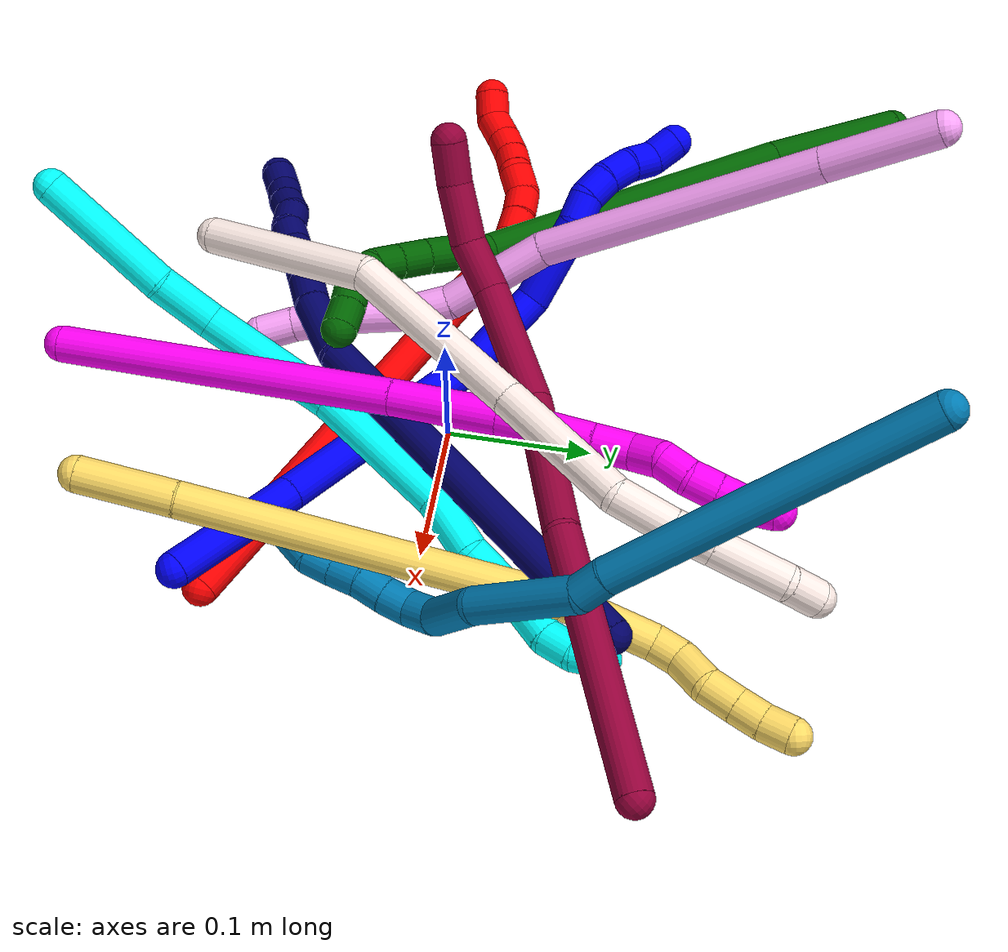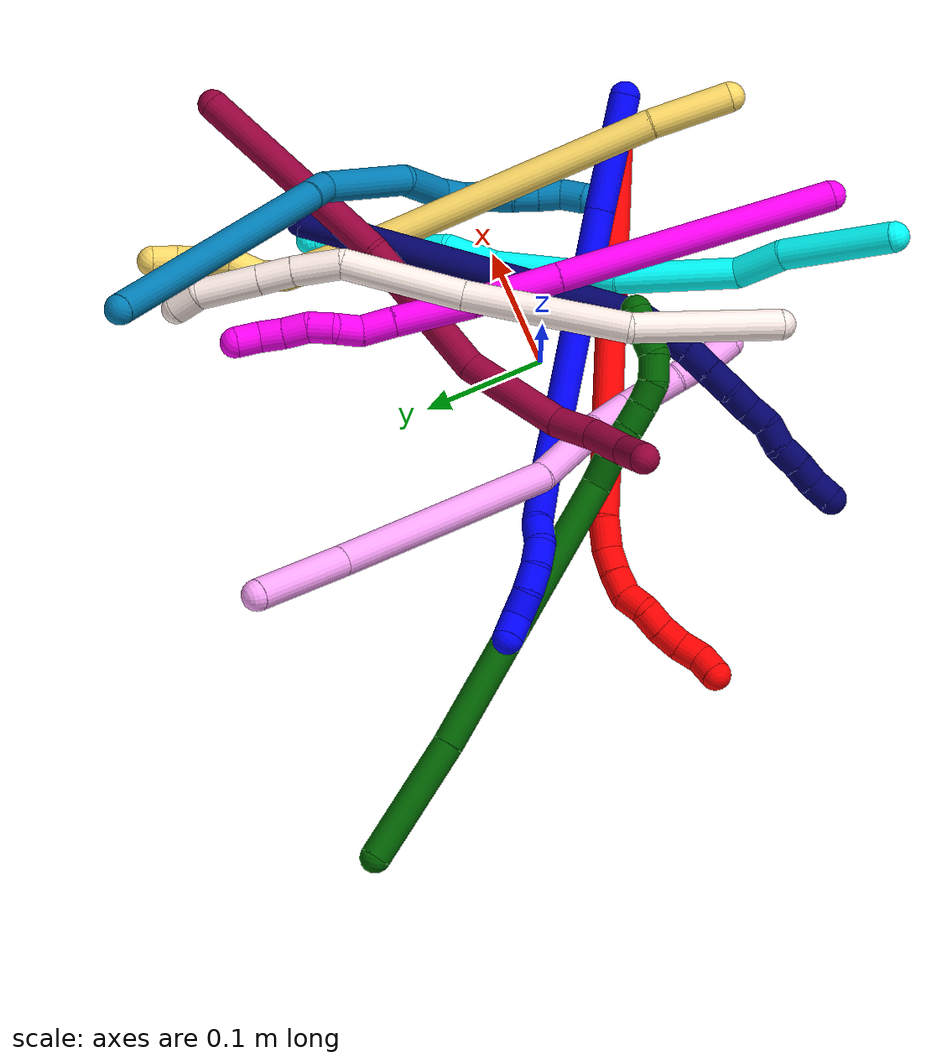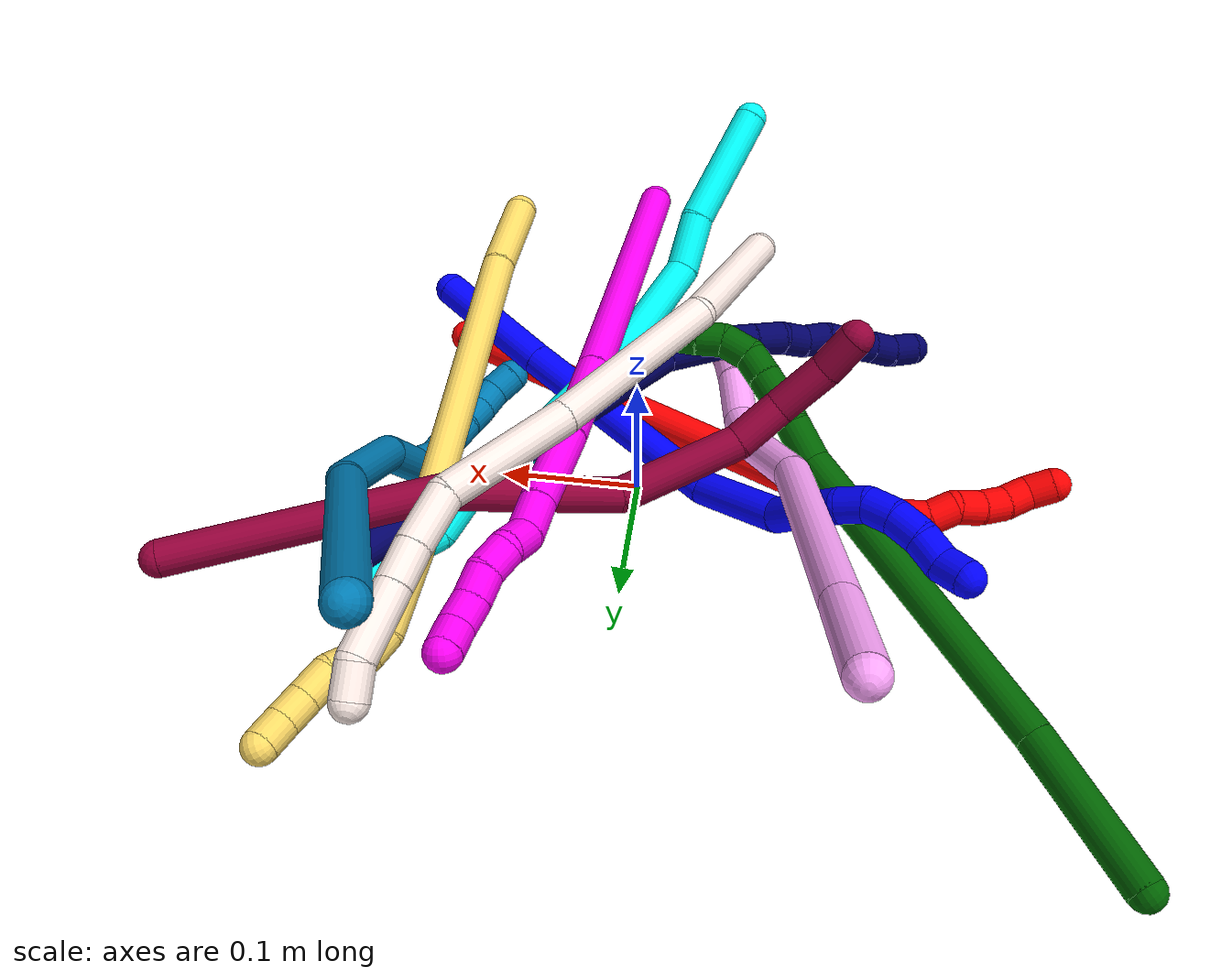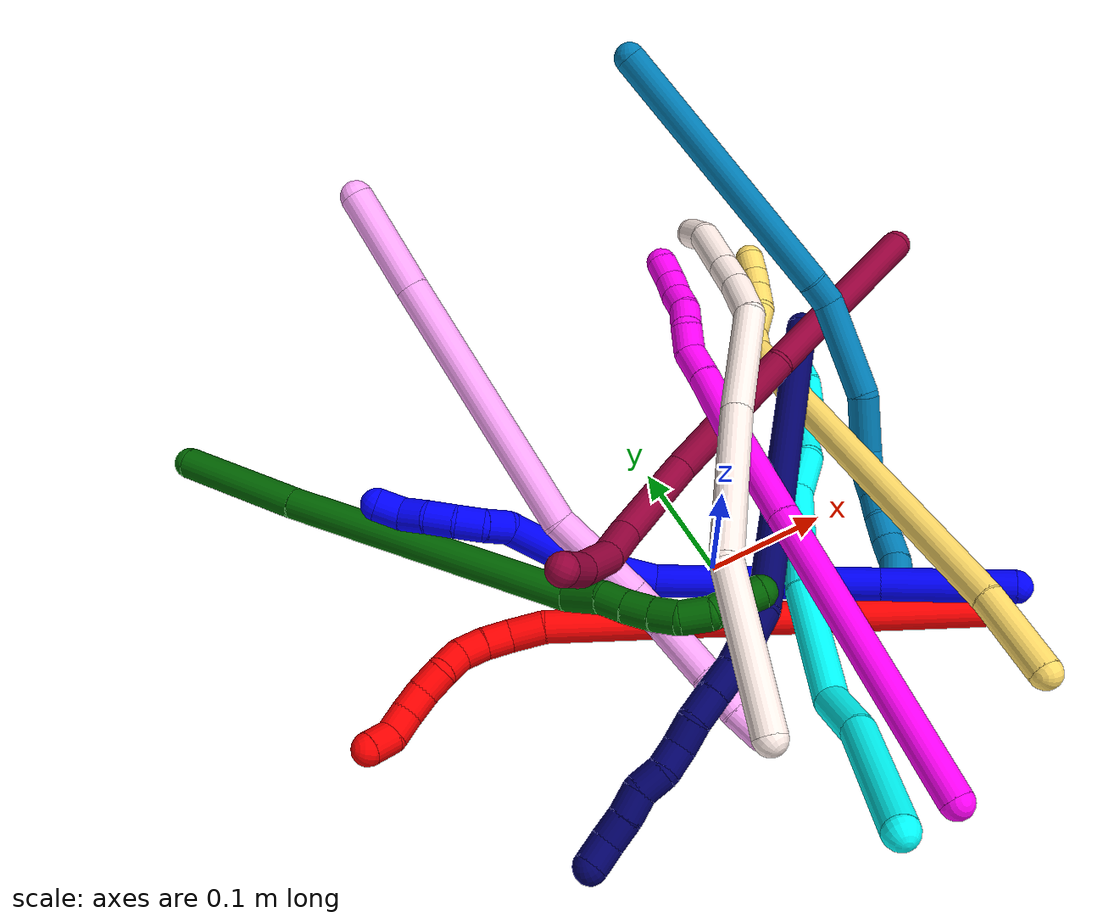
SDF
<sdf version="1.7">
 <world name="default">
  <plugin name="TubeGeneratorPlugin" filename="libtube_generator_plugin.so"/>
  <model name="photoneo_s_sensor">
   <static>1</static>
   <pose>0 0 2 1.57079 1.57079 3.14159</pose>
   <link name="link">
    <inertial><mass>0.1</mass></inertial>
    <sensor name="sensor" type="depth">
     <update_rate>30</update_rate>
     <camera>
      <horizontal_fov>1.22</horizontal_fov>
      <image><width>1920</width><height>1200</height><format>B8G8R8</format></image>
      <clip><near>0.1</near><far>4</far></clip>
      <depth_camera><output>points</output></depth_camera>
     </camera>
     <plugin name="camera_plugin" filename="libgazebo_ros_depth_camera.so">
      <baseline>0.2</baseline>
      <alwaysOn>1</alwaysOn>
      <updateRate>0.0</updateRate>
      <cameraName>camera_ir</cameraName>
      <imageTopicName>/camera/color/image_raw</imageTopicName>
      <cameraInfoTopicName>/camera/color/camera_info</cameraInfoTopicName>
      <depthImageTopicName>/camera/depth/image_raw</depthImageTopicName>
      <depthImageCameraInfoTopicName>/camera/depth/camera_info</depthImageCameraInfoTopicName>
      <pointCloudTopicName>/camera/depth/points</pointCloudTopicName>
      <frameName>fr_optical</frameName>
      <pointCloudCutoff>0.1</pointCloudCutoff>
      <pointCloudCutoffMax>2.0</pointCloudCutoffMax>
      <distortionK1>0</distortionK1>
      <distortionK2>0</distortionK2>
      <distortionK3>0</distortionK3>
      <distortionT1>0</distortionT1>
      <distortionT2>0</distortionT2>
      <CxPrime>0</CxPrime>
      <Cx>0</Cx>
      <Cy>0</Cy>
      <focalLength>0</focalLength>
      <hackBaseline>0</hackBaseline>
     </plugin>
    </sensor>
   </link>
  </model>
  <gravity>0 0 -9.8</gravity>
  <magnetic_field>6e-06 2.3e-05 -4.2e-05</magnetic_field>
  <atmosphere type="adiabatic"/>
  <physics name="default_physics" default="0" type="ode">
   <max_step_size>0.003</max_step_size>
   <real_time_factor>1</real_time_factor>
   <real_time_update_rate>1000</real_time_update_rate>
   <max_contacts>10000</max_contacts>
   <ode>
    <solver>
     <type>quick</type>
     <iters>100</iters>
     <sor>1.3</sor>
     <use_dynamic_moi_rescaling>0</use_dynamic_moi_rescaling>
    </solver>
    <constraints>
     <contact_max_correcting_vel>0</contact_max_correcting_vel>
     <contact_surface_layer>0.001</contact_surface_layer>
     <cfm>0</cfm>
     <erp>0.2</erp>
    </constraints>
   </ode>
  </physics>
  <scene><ambient>0.4 0.4 0.4 1</ambient><background>0.7 0.7 0.7 1</background><shadows>0</shadows></scene>
  <audio><device>default</device></audio>
  <spherical_coordinates>
   <surface_model>EARTH_WGS84</surface_model>
   <latitude_deg>0</latitude_deg>
   <longitude_deg>0</longitude_deg>
   <elevation>0</elevation>
   <heading_deg>0</heading_deg>
  </spherical_coordinates>
  <model name="bin">
   <static>1</static>
   <link name="bottom">
    <collision name="collision-bottom">
     <pose>0 0 -0.01 0 -0 0</pose>
     <geometry><box><size>0.8 0.6 0.02</size></box></geometry>
     <surface>
      <friction><ode><mu>100</mu><mu2>100</mu2></ode></friction>
      <contact><collide_bitmask>65535</collide_bitmask></contact>
     </surface>
    </collision>
   </link>
   <link name="west_wall">
    <collision name="collision-west_wall">
     <pose>-0.41 0 0.1 0 -0 0</pose>
     <geometry><box><size>0.02 0.6 0.2</size></box></geometry>
     <surface>
      <friction><ode><mu>100</mu><mu2>100</mu2></ode></friction>
      <contact><collide_bitmask>65535</collide_bitmask></contact>
     </surface>
    </collision>
   </link>
   <link name="east_wall">
    <collision name="collision-east_wall">
     <pose>0.41 0 0.1 0 -0 0</pose>
     <geometry><box><size>0.02 0.6 0.2</size></box></geometry>
     <surface>
      <friction><ode><mu>100</mu><mu2>100</mu2></ode></friction>
      <contact><collide_bitmask>65535</collide_bitmask></contact>
     </surface>
    </collision>
   </link>
   <link name="south_wall">
    <collision name="collision-south_wall">
     <pose>0 -0.31 0.1 0 -0 0</pose>
     <geometry><box><size>0.8 0.02 0.2</size></box></geometry>
     <surface>
      <friction><ode><mu>100</mu><mu2>100</mu2></ode></friction>
      <contact><collide_bitmask>65535</collide_bitmask></contact>
     </surface>
    </collision>
   </link>
   <link name="north_wall">
    <collision name="collision-north_wall">
     <pose>0 0.31 0.1 0 -0 0</pose>
     <geometry><box><size>0.8 0.02 0.2</size></box></geometry>
     <surface>
      <friction><ode><mu>100</mu><mu2>100</mu2></ode></friction>
      <contact><collide_bitmask>65535</collide_bitmask></contact>
     </surface>
    </collision>
   </link>
  </model>
  <model name="1">
   <static>0</static>
   <link name="1">
    <collision name="collision-cylinder-e_1_1_4">
     <pose>-0.027494 -0.000621 -0.040158 3.12613 -0.600292 -3.09164</pose>
     <geometry><cylinder><radius>0.0125</radius><length>0.097345</length></cylinder></geometry>
     <surface>
      <friction><ode><mu>1.16</mu><mu2>1.16</mu2><slip1>0</slip1><slip2>0</slip2></ode></friction>
      <contact><ode><kp>1e+06</kp><kd>1</kd><max_vel>0</max_vel><min_depth>0.001</min_depth></ode></contact>
     </surface>
    </collision>
    <visual name="visual-cylinder-e_1_1_4">
     <pose>-0.027494 -0.000621 -0.040158 3.12613 -0.600292 -3.09164</pose>
     <geometry><cylinder><radius>0.0125</radius><length>0.097345</length></cylinder></geometry>
     <material><ambient>0 0 1 1</ambient></material>
    </visual>
    <collision name="collision-cylinder-e_2_4_5">
     <pose>-0.103115 -1.5e-05 -0.149817 -3.12394 -0.605572 3.0851</pose>
     <geometry><cylinder><radius>0.0125</radius><length>0.169092</length></cylinder></geometry>
     <surface>
      <friction><ode><mu>1.16</mu><mu2>1.16</mu2><slip1>0</slip1><slip2>0</slip2></ode></friction>
      <contact><ode><kp>1e+06</kp><kd>1</kd><max_vel>0</max_vel><min_depth>0.001</min_depth></ode></contact>
     </surface>
    </collision>
    <visual name="visual-cylinder-e_2_4_5">
     <pose>-0.103115 -1.5e-05 -0.149817 -3.12394 -0.605572 3.0851</pose>
     <geometry><cylinder><radius>0.0125</radius><length>0.169092</length></cylinder></geometry>
     <material><ambient>0 0 1 1</ambient></material>
    </visual>
    <collision name="collision-cylinder-e_3_5_6">
     <pose>-0.163184 0.014 -0.248383 -2.7271 -0.359735 1.42603</pose>
     <geometry><cylinder><radius>0.0125</radius><length>0.06785</length></cylinder></geometry>
     <surface>
      <friction><ode><mu>1.16</mu><mu2>1.16</mu2><slip1>0</slip1><slip2>0</slip2></ode></friction>
      <contact><ode><kp>1e+06</kp><kd>1</kd><max_vel>0</max_vel><min_depth>0.001</min_depth></ode></contact>
     </surface>
    </collision>
    <visual name="visual-cylinder-e_3_5_6">
     <pose>-0.163184 0.014 -0.248383 -2.7271 -0.359735 1.42603</pose>
     <geometry><cylinder><radius>0.0125</radius><length>0.06785</length></cylinder></geometry>
     <material><ambient>0 0 1 1</ambient></material>
    </visual>
    <collision name="collision-cylinder-e_4_6_7">
     <pose>-0.17819 0.048775 -0.299094 -2.34836 -0.098973 0.235421</pose>
     <geometry><cylinder><radius>0.0125</radius><length>0.062012</length></cylinder></geometry>
     <surface>
      <friction><ode><mu>1.16</mu><mu2>1.16</mu2><slip1>0</slip1><slip2>0</slip2></ode></friction>
      <contact><ode><kp>1e+06</kp><kd>1</kd><max_vel>0</max_vel><min_depth>0.001</min_depth></ode></contact>
     </surface>
    </collision>
    <visual name="visual-cylinder-e_4_6_7">
     <pose>-0.17819 0.048775 -0.299094 -2.34836 -0.098973 0.235421</pose>
     <geometry><cylinder><radius>0.0125</radius><length>0.062012</length></cylinder></geometry>
     <material><ambient>0 0 1 1</ambient></material>
    </visual>
    <collision name="collision-cylinder-e_5_7_8">
     <pose>-0.185678 0.077115 -0.327224 -2.36643 -0.453462 1.02875</pose>
     <geometry><cylinder><radius>0.0125</radius><length>0.020196</length></cylinder></geometry>
     <surface>
      <friction><ode><mu>1.16</mu><mu2>1.16</mu2><slip1>0</slip1><slip2>0</slip2></ode></friction>
      <contact><ode><kp>1e+06</kp><kd>1</kd><max_vel>0</max_vel><min_depth>0.001</min_depth></ode></contact>
     </surface>
    </collision>
    <visual name="visual-cylinder-e_5_7_8">
     <pose>-0.185678 0.077115 -0.327224 -2.36643 -0.453462 1.02875</pose>
     <geometry><cylinder><radius>0.0125</radius><length>0.020196</length></cylinder></geometry>
     <material><ambient>0 0 1 1</ambient></material>
    </visual>
    <collision name="collision-cylinder-e_6_8_9">
     <pose>-0.194793 0.086236 -0.342417 -2.83385 -0.47427 2.00051</pose>
     <geometry><cylinder><radius>0.0125</radius><length>0.020546</length></cylinder></geometry>
     <surface>
      <friction><ode><mu>1.16</mu><mu2>1.16</mu2><slip1>0</slip1><slip2>0</slip2></ode></friction>
      <contact><ode><kp>1e+06</kp><kd>1</kd><max_vel>0</max_vel><min_depth>0.001</min_depth></ode></contact>
     </surface>
    </collision>
    <visual name="visual-cylinder-e_6_8_9">
     <pose>-0.194793 0.086236 -0.342417 -2.83385 -0.47427 2.00051</pose>
     <geometry><cylinder><radius>0.0125</radius><length>0.020546</length></cylinder></geometry>
     <material><ambient>0 0 1 1</ambient></material>
    </visual>
    <collision name="collision-cylinder-e_7_9_10">
     <pose>-0.204243 0.089437 -0.36063 -3.0961 -0.463833 2.9495</pose>
     <geometry><cylinder><radius>0.0125</radius><length>0.021275</length></cylinder></geometry>
     <surface>
      <friction><ode><mu>1.16</mu><mu2>1.16</mu2><slip1>0</slip1><slip2>0</slip2></ode></friction>
      <contact><ode><kp>1e+06</kp><kd>1</kd><max_vel>0</max_vel><min_depth>0.001</min_depth></ode></contact>
     </surface>
    </collision>
    <visual name="visual-cylinder-e_7_9_10">
     <pose>-0.204243 0.089437 -0.36063 -3.0961 -0.463833 2.9495</pose>
     <geometry><cylinder><radius>0.0125</radius><length>0.021275</length></cylinder></geometry>
     <material><ambient>0 0 1 1</ambient></material>
    </visual>
    <collision name="collision-cylinder-e_8_10_11">
     <pose>-0.213751 0.087593 -0.379315 2.89847 -0.465323 -2.18955</pose>
     <geometry><cylinder><radius>0.0125</radius><length>0.021168</length></cylinder></geometry>
     <surface>
      <friction><ode><mu>1.16</mu><mu2>1.16</mu2><slip1>0</slip1><slip2>0</slip2></ode></friction>
      <contact><ode><kp>1e+06</kp><kd>1</kd><max_vel>0</max_vel><min_depth>0.001</min_depth></ode></contact>
     </surface>
    </collision>
    <visual name="visual-cylinder-e_8_10_11">
     <pose>-0.213751 0.087593 -0.379315 2.89847 -0.465323 -2.18955</pose>
     <geometry><cylinder><radius>0.0125</radius><length>0.021168</length></cylinder></geometry>
     <material><ambient>0 0 1 1</ambient></material>
    </visual>
    <collision name="collision-cylinder-e_9_11_2">
     <pose>-0.221217 0.087834 -0.398061 -2.88418 -0.267983 1.61148</pose>
     <geometry><cylinder><radius>0.0125</radius><length>0.020516</length></cylinder></geometry>
     <surface>
      <friction><ode><mu>1.16</mu><mu2>1.16</mu2><slip1>0</slip1><slip2>0</slip2></ode></friction>
      <contact><ode><kp>1e+06</kp><kd>1</kd><max_vel>0</max_vel><min_depth>0.001</min_depth></ode></contact>
     </surface>
    </collision>
    <visual name="visual-cylinder-e_9_11_2">
     <pose>-0.221217 0.087834 -0.398061 -2.88418 -0.267983 1.61148</pose>
     <geometry><cylinder><radius>0.0125</radius><length>0.020516</length></cylinder></geometry>
     <material><ambient>0 0 1 1</ambient></material>
    </visual>
    <collision name="collision-sphere-2">
     <pose>-0.223933 0.090352 -0.407627 0 -0 0</pose>
     <geometry><sphere><radius>0.0125</radius></sphere></geometry>
     <surface>
      <friction><ode><mu>1.16</mu><mu2>1.16</mu2><slip1>0</slip1><slip2>0</slip2></ode></friction>
      <contact><ode><kp>1e+06</kp><kd>1</kd><max_vel>0</max_vel><min_depth>0.001</min_depth></ode></contact>
     </surface>
    </collision>
    <visual name="visual-sphere-2">
     <pose>-0.223933 0.090352 -0.407627 0 -0 0</pose>
     <geometry><sphere><radius>0.0125</radius></sphere></geometry>
     <material><ambient>0 0 1 1</ambient></material>
    </visual>
    <collision name="collision-sphere-11">
     <pose>-0.2185 0.085316 -0.388495 0 -0 0</pose>
     <geometry><sphere><radius>0.0125</radius></sphere></geometry>
     <surface>
      <friction><ode><mu>1.16</mu><mu2>1.16</mu2><slip1>0</slip1><slip2>0</slip2></ode></friction>
      <contact><ode><kp>1e+06</kp><kd>1</kd><max_vel>0</max_vel><min_depth>0.001</min_depth></ode></contact>
     </surface>
    </collision>
    <visual name="visual-sphere-11">
     <pose>-0.2185 0.085316 -0.388495 0 -0 0</pose>
     <geometry><sphere><radius>0.0125</radius></sphere></geometry>
     <material><ambient>0 0 1 1</ambient></material>
    </visual>
    <collision name="collision-sphere-10">
     <pose>-0.209002 0.08987 -0.370134 0 -0 0</pose>
     <geometry><sphere><radius>0.0125</radius></sphere></geometry>
     <surface>
      <friction><ode><mu>1.16</mu><mu2>1.16</mu2><slip1>0</slip1><slip2>0</slip2></ode></friction>
      <contact><ode><kp>1e+06</kp><kd>1</kd><max_vel>0</max_vel><min_depth>0.001</min_depth></ode></contact>
     </surface>
    </collision>
    <visual name="visual-sphere-10">
     <pose>-0.209002 0.08987 -0.370134 0 -0 0</pose>
     <geometry><sphere><radius>0.0125</radius></sphere></geometry>
     <material><ambient>0 0 1 1</ambient></material>
    </visual>
    <collision name="collision-sphere-9">
     <pose>-0.199484 0.089005 -0.351127 0 -0 0</pose>
     <geometry><sphere><radius>0.0125</radius></sphere></geometry>
     <surface>
      <friction><ode><mu>1.16</mu><mu2>1.16</mu2><slip1>0</slip1><slip2>0</slip2></ode></friction>
      <contact><ode><kp>1e+06</kp><kd>1</kd><max_vel>0</max_vel><min_depth>0.001</min_depth></ode></contact>
     </surface>
    </collision>
    <visual name="visual-sphere-9">
     <pose>-0.199484 0.089005 -0.351127 0 -0 0</pose>
     <geometry><sphere><radius>0.0125</radius></sphere></geometry>
     <material><ambient>0 0 1 1</ambient></material>
    </visual>
    <collision name="collision-sphere-4">
     <pose>-0.054988 -0.001242 -0.080316 0 -0 0</pose>
     <geometry><sphere><radius>0.0125</radius></sphere></geometry>
     <surface>
      <friction><ode><mu>1.16</mu><mu2>1.16</mu2><slip1>0</slip1><slip2>0</slip2></ode></friction>
      <contact><ode><kp>1e+06</kp><kd>1</kd><max_vel>0</max_vel><min_depth>0.001</min_depth></ode></contact>
     </surface>
    </collision>
    <visual name="visual-sphere-4">
     <pose>-0.054988 -0.001242 -0.080316 0 -0 0</pose>
     <geometry><sphere><radius>0.0125</radius></sphere></geometry>
     <material><ambient>0 0 1 1</ambient></material>
    </visual>
    <collision name="collision-sphere-1">
     <geometry><sphere><radius>0.0125</radius></sphere></geometry>
     <surface>
      <friction><ode><mu>1.16</mu><mu2>1.16</mu2><slip1>0</slip1><slip2>0</slip2></ode></friction>
      <contact><ode><kp>1e+06</kp><kd>1</kd><max_vel>0</max_vel><min_depth>0.001</min_depth></ode></contact>
     </surface>
    </collision>
    <visual name="visual-sphere-1">
     <geometry><sphere><radius>0.0125</radius></sphere></geometry>
     <material><ambient>0 0 1 1</ambient></material>
    </visual>
    <collision name="collision-sphere-8">
     <pose>-0.190101 0.083468 -0.333708 0 -0 0</pose>
     <geometry><sphere><radius>0.0125</radius></sphere></geometry>
     <surface>
      <friction><ode><mu>1.16</mu><mu2>1.16</mu2><slip1>0</slip1><slip2>0</slip2></ode></friction>
      <contact><ode><kp>1e+06</kp><kd>1</kd><max_vel>0</max_vel><min_depth>0.001</min_depth></ode></contact>
     </surface>
    </collision>
    <visual name="visual-sphere-8">
     <pose>-0.190101 0.083468 -0.333708 0 -0 0</pose>
     <geometry><sphere><radius>0.0125</radius></sphere></geometry>
     <material><ambient>0 0 1 1</ambient></material>
    </visual>
    <collision name="collision-sphere-5">
     <pose>-0.151241 0.001212 -0.219319 0 -0 0</pose>
     <geometry><sphere><radius>0.0125</radius></sphere></geometry>
     <surface>
      <friction><ode><mu>1.16</mu><mu2>1.16</mu2><slip1>0</slip1><slip2>0</slip2></ode></friction>
      <contact><ode><kp>1e+06</kp><kd>1</kd><max_vel>0</max_vel><min_depth>0.001</min_depth></ode></contact>
     </surface>
    </collision>
    <visual name="visual-sphere-5">
     <pose>-0.151241 0.001212 -0.219319 0 -0 0</pose>
     <geometry><sphere><radius>0.0125</radius></sphere></geometry>
     <material><ambient>0 0 1 1</ambient></material>
    </visual>
    <collision name="collision-sphere-6">
     <pose>-0.175126 0.026788 -0.277448 0 -0 0</pose>
     <geometry><sphere><radius>0.0125</radius></sphere></geometry>
     <surface>
      <friction><ode><mu>1.16</mu><mu2>1.16</mu2><slip1>0</slip1><slip2>0</slip2></ode></friction>
      <contact><ode><kp>1e+06</kp><kd>1</kd><max_vel>0</max_vel><min_depth>0.001</min_depth></ode></contact>
     </surface>
    </collision>
    <visual name="visual-sphere-6">
     <pose>-0.175126 0.026788 -0.277448 0 -0 0</pose>
     <geometry><sphere><radius>0.0125</radius></sphere></geometry>
     <material><ambient>0 0 1 1</ambient></material>
    </visual>
    <collision name="collision-sphere-7">
     <pose>-0.181254 0.070763 -0.32074 0 -0 0</pose>
     <geometry><sphere><radius>0.0125</radius></sphere></geometry>
     <surface>
      <friction><ode><mu>1.16</mu><mu2>1.16</mu2><slip1>0</slip1><slip2>0</slip2></ode></friction>
      <contact><ode><kp>1e+06</kp><kd>1</kd><max_vel>0</max_vel><min_depth>0.001</min_depth></ode></contact>
     </surface>
    </collision>
    <visual name="visual-sphere-7">
     <pose>-0.181254 0.070763 -0.32074 0 -0 0</pose>
     <geometry><sphere><radius>0.0125</radius></sphere></geometry>
     <material><ambient>0 0 1 1</ambient></material>
    </visual>
    <inertial>
     <pose>-0.12679 0.025599 -0.204309 0 -0 0</pose>
     <mass>0.5</mass>
     <inertia>
      <ixx>-0.000347</ixx>
      <ixy>0</ixy>
      <ixz>0</ixz>
      <iyy>0.000536</iyy>
      <iyz>0</iyz>
      <izz>0.000229</izz>
     </inertia>
    </inertial>
   </link>
   <pose>0.166823 -0.145708 0.050951 1.73412 -0.495328 0.352187</pose>
  </model>
  <model name="2">
   <static>0</static>
   <link name="2">
    <collision name="collision-cylinder-e_1_1_4">
     <pose>-0.080131 0.049576 0.136875 -0.347501 -0.503177 0.090169</pose>
     <geometry><cylinder><radius>0.0125</radius><length>0.332347</length></cylinder></geometry>
     <surface>
      <friction><ode><mu>1.16</mu><mu2>1.16</mu2><slip1>0</slip1><slip2>0</slip2></ode></friction>
      <contact><ode><kp>1e+06</kp><kd>1</kd><max_vel>0</max_vel><min_depth>0.001</min_depth></ode></contact>
     </surface>
    </collision>
    <visual name="visual-cylinder-e_1_1_4">
     <pose>-0.080131 0.049576 0.136875 -0.347501 -0.503177 0.090169</pose>
     <geometry><cylinder><radius>0.0125</radius><length>0.332347</length></cylinder></geometry>
     <material><ambient>1 0 0 1</ambient></material>
    </visual>
    <collision name="collision-cylinder-e_2_4_5">
     <pose>-0.16881 0.101143 0.283802 -0.195548 -0.695318 0.071059</pose>
     <geometry><cylinder><radius>0.0125</radius><length>0.026689</length></cylinder></geometry>
     <surface>
      <friction><ode><mu>1.16</mu><mu2>1.16</mu2><slip1>0</slip1><slip2>0</slip2></ode></friction>
      <contact><ode><kp>1e+06</kp><kd>1</kd><max_vel>0</max_vel><min_depth>0.001</min_depth></ode></contact>
     </surface>
    </collision>
    <visual name="visual-cylinder-e_2_4_5">
     <pose>-0.16881 0.101143 0.283802 -0.195548 -0.695318 0.071059</pose>
     <geometry><cylinder><radius>0.0125</radius><length>0.026689</length></cylinder></geometry>
     <material><ambient>1 0 0 1</ambient></material>
    </visual>
    <collision name="collision-cylinder-e_3_5_6">
     <pose>-0.181832 0.102731 0.303229 0.043017 -0.444792 -0.009729</pose>
     <geometry><cylinder><radius>0.0125</radius><length>0.020793</length></cylinder></geometry>
     <surface>
      <friction><ode><mu>1.16</mu><mu2>1.16</mu2><slip1>0</slip1><slip2>0</slip2></ode></friction>
      <contact><ode><kp>1e+06</kp><kd>1</kd><max_vel>0</max_vel><min_depth>0.001</min_depth></ode></contact>
     </surface>
    </collision>
    <visual name="visual-cylinder-e_3_5_6">
     <pose>-0.181832 0.102731 0.303229 0.043017 -0.444792 -0.009729</pose>
     <geometry><cylinder><radius>0.0125</radius><length>0.020793</length></cylinder></geometry>
     <material><ambient>1 0 0 1</ambient></material>
    </visual>
    <collision name="collision-cylinder-e_4_6_7">
     <pose>-0.191164 0.100769 0.321298 0.177381 -0.502972 -0.045686</pose>
     <geometry><cylinder><radius>0.0125</radius><length>0.020157</length></cylinder></geometry>
     <surface>
      <friction><ode><mu>1.16</mu><mu2>1.16</mu2><slip1>0</slip1><slip2>0</slip2></ode></friction>
      <contact><ode><kp>1e+06</kp><kd>1</kd><max_vel>0</max_vel><min_depth>0.001</min_depth></ode></contact>
     </surface>
    </collision>
    <visual name="visual-cylinder-e_4_6_7">
     <pose>-0.191164 0.100769 0.321298 0.177381 -0.502972 -0.045686</pose>
     <geometry><cylinder><radius>0.0125</radius><length>0.020157</length></cylinder></geometry>
     <material><ambient>1 0 0 1</ambient></material>
    </visual>
    <collision name="collision-cylinder-e_5_7_8">
     <pose>-0.198281 0.093737 0.338049 0.596606 -0.22788 -0.070344</pose>
     <geometry><cylinder><radius>0.0125</radius><length>0.020003</length></cylinder></geometry>
     <surface>
      <friction><ode><mu>1.16</mu><mu2>1.16</mu2><slip1>0</slip1><slip2>0</slip2></ode></friction>
      <contact><ode><kp>1e+06</kp><kd>1</kd><max_vel>0</max_vel><min_depth>0.001</min_depth></ode></contact>
     </surface>
    </collision>
    <visual name="visual-cylinder-e_5_7_8">
     <pose>-0.198281 0.093737 0.338049 0.596606 -0.22788 -0.070344</pose>
     <geometry><cylinder><radius>0.0125</radius><length>0.020003</length></cylinder></geometry>
     <material><ambient>1 0 0 1</ambient></material>
    </visual>
    <collision name="collision-cylinder-e_6_8_9">
     <pose>-0.207145 0.083949 0.35226 0.611589 -0.721109 -0.236943</pose>
     <geometry><cylinder><radius>0.0125</radius><length>0.020006</length></cylinder></geometry>
     <surface>
      <friction><ode><mu>1.16</mu><mu2>1.16</mu2><slip1>0</slip1><slip2>0</slip2></ode></friction>
      <contact><ode><kp>1e+06</kp><kd>1</kd><max_vel>0</max_vel><min_depth>0.001</min_depth></ode></contact>
     </surface>
    </collision>
    <visual name="visual-cylinder-e_6_8_9">
     <pose>-0.207145 0.083949 0.35226 0.611589 -0.721109 -0.236943</pose>
     <geometry><cylinder><radius>0.0125</radius><length>0.020006</length></cylinder></geometry>
     <material><ambient>1 0 0 1</ambient></material>
    </visual>
    <collision name="collision-cylinder-e_7_9_10">
     <pose>-0.219209 0.073955 0.364573 0.744793 -0.577413 -0.231001</pose>
     <geometry><cylinder><radius>0.0125</radius><length>0.020003</length></cylinder></geometry>
     <surface>
      <friction><ode><mu>1.16</mu><mu2>1.16</mu2><slip1>0</slip1><slip2>0</slip2></ode></friction>
      <contact><ode><kp>1e+06</kp><kd>1</kd><max_vel>0</max_vel><min_depth>0.001</min_depth></ode></contact>
     </surface>
    </collision>
    <visual name="visual-cylinder-e_7_9_10">
     <pose>-0.219209 0.073955 0.364573 0.744793 -0.577413 -0.231001</pose>
     <geometry><cylinder><radius>0.0125</radius><length>0.020003</length></cylinder></geometry>
     <material><ambient>1 0 0 1</ambient></material>
    </visual>
    <collision name="collision-cylinder-e_8_10_11">
     <pose>-0.228115 0.06157 0.377305 0.79552 -0.3519 -0.149121</pose>
     <geometry><cylinder><radius>0.0125</radius><length>0.020001</length></cylinder></geometry>
     <surface>
      <friction><ode><mu>1.16</mu><mu2>1.16</mu2><slip1>0</slip1><slip2>0</slip2></ode></friction>
      <contact><ode><kp>1e+06</kp><kd>1</kd><max_vel>0</max_vel><min_depth>0.001</min_depth></ode></contact>
     </surface>
    </collision>
    <visual name="visual-cylinder-e_8_10_11">
     <pose>-0.228115 0.06157 0.377305 0.79552 -0.3519 -0.149121</pose>
     <geometry><cylinder><radius>0.0125</radius><length>0.020001</length></cylinder></geometry>
     <material><ambient>1 0 0 1</ambient></material>
    </visual>
    <collision name="collision-cylinder-e_9_11_2">
     <pose>-0.233392 0.051394 0.393074 0.360798 -0.183963 -0.033643</pose>
     <geometry><cylinder><radius>0.0125</radius><length>0.020001</length></cylinder></geometry>
     <surface>
      <friction><ode><mu>1.16</mu><mu2>1.16</mu2><slip1>0</slip1><slip2>0</slip2></ode></friction>
      <contact><ode><kp>1e+06</kp><kd>1</kd><max_vel>0</max_vel><min_depth>0.001</min_depth></ode></contact>
     </surface>
    </collision>
    <visual name="visual-cylinder-e_9_11_2">
     <pose>-0.233392 0.051394 0.393074 0.360798 -0.183963 -0.033643</pose>
     <geometry><cylinder><radius>0.0125</radius><length>0.020001</length></cylinder></geometry>
     <material><ambient>1 0 0 1</ambient></material>
    </visual>
    <collision name="collision-sphere-2">
     <pose>-0.235221 0.047923 0.402272 0 -0 0</pose>
     <geometry><sphere><radius>0.0125</radius></sphere></geometry>
     <surface>
      <friction><ode><mu>1.16</mu><mu2>1.16</mu2><slip1>0</slip1><slip2>0</slip2></ode></friction>
      <contact><ode><kp>1e+06</kp><kd>1</kd><max_vel>0</max_vel><min_depth>0.001</min_depth></ode></contact>
     </surface>
    </collision>
    <visual name="visual-sphere-2">
     <pose>-0.235221 0.047923 0.402272 0 -0 0</pose>
     <geometry><sphere><radius>0.0125</radius></sphere></geometry>
     <material><ambient>1 0 0 1</ambient></material>
    </visual>
    <collision name="collision-sphere-11">
     <pose>-0.231562 0.054865 0.383875 0 -0 0</pose>
     <geometry><sphere><radius>0.0125</radius></sphere></geometry>
     <surface>
      <friction><ode><mu>1.16</mu><mu2>1.16</mu2><slip1>0</slip1><slip2>0</slip2></ode></friction>
      <contact><ode><kp>1e+06</kp><kd>1</kd><max_vel>0</max_vel><min_depth>0.001</min_depth></ode></contact>
     </surface>
    </collision>
    <visual name="visual-sphere-11">
     <pose>-0.231562 0.054865 0.383875 0 -0 0</pose>
     <geometry><sphere><radius>0.0125</radius></sphere></geometry>
     <material><ambient>1 0 0 1</ambient></material>
    </visual>
    <collision name="collision-sphere-10">
     <pose>-0.224668 0.068275 0.370734 0 -0 0</pose>
     <geometry><sphere><radius>0.0125</radius></sphere></geometry>
     <surface>
      <friction><ode><mu>1.16</mu><mu2>1.16</mu2><slip1>0</slip1><slip2>0</slip2></ode></friction>
      <contact><ode><kp>1e+06</kp><kd>1</kd><max_vel>0</max_vel><min_depth>0.001</min_depth></ode></contact>
     </surface>
    </collision>
    <visual name="visual-sphere-10">
     <pose>-0.224668 0.068275 0.370734 0 -0 0</pose>
     <geometry><sphere><radius>0.0125</radius></sphere></geometry>
     <material><ambient>1 0 0 1</ambient></material>
    </visual>
    <collision name="collision-sphere-9">
     <pose>-0.213749 0.079635 0.358412 0 -0 0</pose>
     <geometry><sphere><radius>0.0125</radius></sphere></geometry>
     <surface>
      <friction><ode><mu>1.16</mu><mu2>1.16</mu2><slip1>0</slip1><slip2>0</slip2></ode></friction>
      <contact><ode><kp>1e+06</kp><kd>1</kd><max_vel>0</max_vel><min_depth>0.001</min_depth></ode></contact>
     </surface>
    </collision>
    <visual name="visual-sphere-9">
     <pose>-0.213749 0.079635 0.358412 0 -0 0</pose>
     <geometry><sphere><radius>0.0125</radius></sphere></geometry>
     <material><ambient>1 0 0 1</ambient></material>
    </visual>
    <collision name="collision-sphere-4">
     <pose>-0.160261 0.099152 0.273751 0 -0 0</pose>
     <geometry><sphere><radius>0.0125</radius></sphere></geometry>
     <surface>
      <friction><ode><mu>1.16</mu><mu2>1.16</mu2><slip1>0</slip1><slip2>0</slip2></ode></friction>
      <contact><ode><kp>1e+06</kp><kd>1</kd><max_vel>0</max_vel><min_depth>0.001</min_depth></ode></contact>
     </surface>
    </collision>
    <visual name="visual-sphere-4">
     <pose>-0.160261 0.099152 0.273751 0 -0 0</pose>
     <geometry><sphere><radius>0.0125</radius></sphere></geometry>
     <material><ambient>1 0 0 1</ambient></material>
    </visual>
    <collision name="collision-sphere-1">
     <geometry><sphere><radius>0.0125</radius></sphere></geometry>
     <surface>
      <friction><ode><mu>1.16</mu><mu2>1.16</mu2><slip1>0</slip1><slip2>0</slip2></ode></friction>
      <contact><ode><kp>1e+06</kp><kd>1</kd><max_vel>0</max_vel><min_depth>0.001</min_depth></ode></contact>
     </surface>
    </collision>
    <visual name="visual-sphere-1">
     <geometry><sphere><radius>0.0125</radius></sphere></geometry>
     <material><ambient>1 0 0 1</ambient></material>
    </visual>
    <collision name="collision-sphere-8">
     <pose>-0.200541 0.088263 0.346109 0 -0 0</pose>
     <geometry><sphere><radius>0.0125</radius></sphere></geometry>
     <surface>
      <friction><ode><mu>1.16</mu><mu2>1.16</mu2><slip1>0</slip1><slip2>0</slip2></ode></friction>
      <contact><ode><kp>1e+06</kp><kd>1</kd><max_vel>0</max_vel><min_depth>0.001</min_depth></ode></contact>
     </surface>
    </collision>
    <visual name="visual-sphere-8">
     <pose>-0.200541 0.088263 0.346109 0 -0 0</pose>
     <geometry><sphere><radius>0.0125</radius></sphere></geometry>
     <material><ambient>1 0 0 1</ambient></material>
    </visual>
    <collision name="collision-sphere-5">
     <pose>-0.177359 0.103134 0.293853 0 -0 0</pose>
     <geometry><sphere><radius>0.0125</radius></sphere></geometry>
     <surface>
      <friction><ode><mu>1.16</mu><mu2>1.16</mu2><slip1>0</slip1><slip2>0</slip2></ode></friction>
      <contact><ode><kp>1e+06</kp><kd>1</kd><max_vel>0</max_vel><min_depth>0.001</min_depth></ode></contact>
     </surface>
    </collision>
    <visual name="visual-sphere-5">
     <pose>-0.177359 0.103134 0.293853 0 -0 0</pose>
     <geometry><sphere><radius>0.0125</radius></sphere></geometry>
     <material><ambient>1 0 0 1</ambient></material>
    </visual>
    <collision name="collision-sphere-6">
     <pose>-0.186306 0.102327 0.312606 0 -0 0</pose>
     <geometry><sphere><radius>0.0125</radius></sphere></geometry>
     <surface>
      <friction><ode><mu>1.16</mu><mu2>1.16</mu2><slip1>0</slip1><slip2>0</slip2></ode></friction>
      <contact><ode><kp>1e+06</kp><kd>1</kd><max_vel>0</max_vel><min_depth>0.001</min_depth></ode></contact>
     </surface>
    </collision>
    <visual name="visual-sphere-6">
     <pose>-0.186306 0.102327 0.312606 0 -0 0</pose>
     <geometry><sphere><radius>0.0125</radius></sphere></geometry>
     <material><ambient>1 0 0 1</ambient></material>
    </visual>
    <collision name="collision-sphere-7">
     <pose>-0.196022 0.099211 0.329989 0 -0 0</pose>
     <geometry><sphere><radius>0.0125</radius></sphere></geometry>
     <surface>
      <friction><ode><mu>1.16</mu><mu2>1.16</mu2><slip1>0</slip1><slip2>0</slip2></ode></friction>
      <contact><ode><kp>1e+06</kp><kd>1</kd><max_vel>0</max_vel><min_depth>0.001</min_depth></ode></contact>
     </surface>
    </collision>
    <visual name="visual-sphere-7">
     <pose>-0.196022 0.099211 0.329989 0 -0 0</pose>
     <geometry><sphere><radius>0.0125</radius></sphere></geometry>
     <material><ambient>1 0 0 1</ambient></material>
    </visual>
    <inertial>
     <pose>-0.120993 0.061273 0.204712 0 -0 0</pose>
     <mass>0.5</mass>
     <inertia>
      <ixx>0.002915</ixx>
      <ixy>0</ixy>
      <ixz>0</ixz>
      <iyy>0.003179</iyy>
      <iyz>0</iyz>
      <izz>0.000606</izz>
     </inertia>
    </inertial>
   </link>
   <pose>0.155756 -0.135963 0.011494 -0.027209 -1.02216 -0.120982</pose>
  </model>
  <model name="3">
   <static>0</static>
   <link name="3">
    <collision name="collision-cylinder-e_1_1_4">
     <pose>0.009274 -0.003301 -0.046771 3.07112 0.195273 2.45071</pose>
     <geometry><cylinder><radius>0.0125</radius><length>0.095592</length></cylinder></geometry>
     <surface>
      <friction><ode><mu>1.16</mu><mu2>1.16</mu2><slip1>0</slip1><slip2>0</slip2></ode></friction>
      <contact><ode><kp>1e+06</kp><kd>1</kd><max_vel>0</max_vel><min_depth>0.001</min_depth></ode></contact>
     </surface>
    </collision>
    <visual name="visual-cylinder-e_1_1_4">
     <pose>0.009274 -0.003301 -0.046771 3.07112 0.195273 2.45071</pose>
     <geometry><cylinder><radius>0.0125</radius><length>0.095592</length></cylinder></geometry>
     <material><ambient>0.003922 1 0.996078 1</ambient></material>
    </visual>
    <collision name="collision-cylinder-e_2_4_5">
     <pose>0.021694 -0.012621 -0.114263 2.85893 0.144792 0.94279</pose>
     <geometry><cylinder><radius>0.0125</radius><length>0.04361</length></cylinder></geometry>
     <surface>
      <friction><ode><mu>1.16</mu><mu2>1.16</mu2><slip1>0</slip1><slip2>0</slip2></ode></friction>
      <contact><ode><kp>1e+06</kp><kd>1</kd><max_vel>0</max_vel><min_depth>0.001</min_depth></ode></contact>
     </surface>
    </collision>
    <visual name="visual-cylinder-e_2_4_5">
     <pose>0.021694 -0.012621 -0.114263 2.85893 0.144792 0.94279</pose>
     <geometry><cylinder><radius>0.0125</radius><length>0.04361</length></cylinder></geometry>
     <material><ambient>0.003922 1 0.996078 1</ambient></material>
    </visual>
    <collision name="collision-cylinder-e_3_5_6">
     <pose>0.025186 -0.010293 -0.183752 -2.9721 0.006976 -0.082069</pose>
     <geometry><cylinder><radius>0.0125</radius><length>0.098958</length></cylinder></geometry>
     <surface>
      <friction><ode><mu>1.16</mu><mu2>1.16</mu2><slip1>0</slip1><slip2>0</slip2></ode></friction>
      <contact><ode><kp>1e+06</kp><kd>1</kd><max_vel>0</max_vel><min_depth>0.001</min_depth></ode></contact>
     </surface>
    </collision>
    <visual name="visual-cylinder-e_3_5_6">
     <pose>0.025186 -0.010293 -0.183752 -2.9721 0.006976 -0.082069</pose>
     <geometry><cylinder><radius>0.0125</radius><length>0.098958</length></cylinder></geometry>
     <material><ambient>0.003922 1 0.996078 1</ambient></material>
    </visual>
    <collision name="collision-cylinder-e_4_6_7">
     <pose>0.03208 0.011225 -0.280366 -2.87295 0.131211 -0.905072</pose>
     <geometry><cylinder><radius>0.0125</radius><length>0.100111</length></cylinder></geometry>
     <surface>
      <friction><ode><mu>1.16</mu><mu2>1.16</mu2><slip1>0</slip1><slip2>0</slip2></ode></friction>
      <contact><ode><kp>1e+06</kp><kd>1</kd><max_vel>0</max_vel><min_depth>0.001</min_depth></ode></contact>
     </surface>
    </collision>
    <visual name="visual-cylinder-e_4_6_7">
     <pose>0.03208 0.011225 -0.280366 -2.87295 0.131211 -0.905072</pose>
     <geometry><cylinder><radius>0.0125</radius><length>0.100111</length></cylinder></geometry>
     <material><ambient>0.003922 1 0.996078 1</ambient></material>
    </visual>
    <collision name="collision-cylinder-e_5_7_8">
     <pose>0.045021 0.032934 -0.346704 -2.70906 0.304091 -1.218</pose>
     <geometry><cylinder><radius>0.0125</radius><length>0.042695</length></cylinder></geometry>
     <surface>
      <friction><ode><mu>1.16</mu><mu2>1.16</mu2><slip1>0</slip1><slip2>0</slip2></ode></friction>
      <contact><ode><kp>1e+06</kp><kd>1</kd><max_vel>0</max_vel><min_depth>0.001</min_depth></ode></contact>
     </surface>
    </collision>
    <visual name="visual-cylinder-e_5_7_8">
     <pose>0.045021 0.032934 -0.346704 -2.70906 0.304091 -1.218</pose>
     <geometry><cylinder><radius>0.0125</radius><length>0.042695</length></cylinder></geometry>
     <material><ambient>0.003922 1 0.996078 1</ambient></material>
    </visual>
    <collision name="collision-cylinder-e_6_8_9">
     <pose>0.057024 0.042229 -0.387592 -3.10782 0.245353 -2.86932</pose>
     <geometry><cylinder><radius>0.0125</radius><length>0.046201</length></cylinder></geometry>
     <surface>
      <friction><ode><mu>1.16</mu><mu2>1.16</mu2><slip1>0</slip1><slip2>0</slip2></ode></friction>
      <contact><ode><kp>1e+06</kp><kd>1</kd><max_vel>0</max_vel><min_depth>0.001</min_depth></ode></contact>
     </surface>
    </collision>
    <visual name="visual-cylinder-e_6_8_9">
     <pose>0.057024 0.042229 -0.387592 -3.10782 0.245353 -2.86932</pose>
     <geometry><cylinder><radius>0.0125</radius><length>0.046201</length></cylinder></geometry>
     <material><ambient>0.003922 1 0.996078 1</ambient></material>
    </visual>
    <collision name="collision-cylinder-e_7_9_10">
     <pose>0.065696 0.051062 -0.42319 -2.59259 0.195268 -0.669439</pose>
     <geometry><cylinder><radius>0.0125</radius><length>0.031553</length></cylinder></geometry>
     <surface>
      <friction><ode><mu>1.16</mu><mu2>1.16</mu2><slip1>0</slip1><slip2>0</slip2></ode></friction>
      <contact><ode><kp>1e+06</kp><kd>1</kd><max_vel>0</max_vel><min_depth>0.001</min_depth></ode></contact>
     </surface>
    </collision>
    <visual name="visual-cylinder-e_7_9_10">
     <pose>0.065696 0.051062 -0.42319 -2.59259 0.195268 -0.669439</pose>
     <geometry><cylinder><radius>0.0125</radius><length>0.031553</length></cylinder></geometry>
     <material><ambient>0.003922 1 0.996078 1</ambient></material>
    </visual>
    <collision name="collision-cylinder-e_8_10_11">
     <pose>0.067379 0.063485 -0.446001 -2.71679 -0.129927 0.585965</pose>
     <geometry><cylinder><radius>0.0125</radius><length>0.021272</length></cylinder></geometry>
     <surface>
      <friction><ode><mu>1.16</mu><mu2>1.16</mu2><slip1>0</slip1><slip2>0</slip2></ode></friction>
      <contact><ode><kp>1e+06</kp><kd>1</kd><max_vel>0</max_vel><min_depth>0.001</min_depth></ode></contact>
     </surface>
    </collision>
    <visual name="visual-cylinder-e_8_10_11">
     <pose>0.067379 0.063485 -0.446001 -2.71679 -0.129927 0.585965</pose>
     <geometry><cylinder><radius>0.0125</radius><length>0.021272</length></cylinder></geometry>
     <material><ambient>0.003922 1 0.996078 1</ambient></material>
    </visual>
    <collision name="collision-cylinder-e_9_11_2">
     <pose>0.06203 0.069919 -0.464552 -2.91217 -0.408192 2.1257</pose>
     <geometry><cylinder><radius>0.0125</radius><length>0.020009</length></cylinder></geometry>
     <surface>
      <friction><ode><mu>1.16</mu><mu2>1.16</mu2><slip1>0</slip1><slip2>0</slip2></ode></friction>
      <contact><ode><kp>1e+06</kp><kd>1</kd><max_vel>0</max_vel><min_depth>0.001</min_depth></ode></contact>
     </surface>
    </collision>
    <visual name="visual-cylinder-e_9_11_2">
     <pose>0.06203 0.069919 -0.464552 -2.91217 -0.408192 2.1257</pose>
     <geometry><cylinder><radius>0.0125</radius><length>0.020009</length></cylinder></geometry>
     <material><ambient>0.003922 1 0.996078 1</ambient></material>
    </visual>
    <collision name="collision-sphere-2">
     <pose>0.058059 0.072008 -0.473494 0 -0 0</pose>
     <geometry><sphere><radius>0.0125</radius></sphere></geometry>
     <surface>
      <friction><ode><mu>1.16</mu><mu2>1.16</mu2><slip1>0</slip1><slip2>0</slip2></ode></friction>
      <contact><ode><kp>1e+06</kp><kd>1</kd><max_vel>0</max_vel><min_depth>0.001</min_depth></ode></contact>
     </surface>
    </collision>
    <visual name="visual-sphere-2">
     <pose>0.058059 0.072008 -0.473494 0 -0 0</pose>
     <geometry><sphere><radius>0.0125</radius></sphere></geometry>
     <material><ambient>0.003922 1 0.996078 1</ambient></material>
    </visual>
    <collision name="collision-sphere-11">
     <pose>0.066001 0.067831 -0.45561 0 -0 0</pose>
     <geometry><sphere><radius>0.0125</radius></sphere></geometry>
     <surface>
      <friction><ode><mu>1.16</mu><mu2>1.16</mu2><slip1>0</slip1><slip2>0</slip2></ode></friction>
      <contact><ode><kp>1e+06</kp><kd>1</kd><max_vel>0</max_vel><min_depth>0.001</min_depth></ode></contact>
     </surface>
    </collision>
    <visual name="visual-sphere-11">
     <pose>0.066001 0.067831 -0.45561 0 -0 0</pose>
     <geometry><sphere><radius>0.0125</radius></sphere></geometry>
     <material><ambient>0.003922 1 0.996078 1</ambient></material>
    </visual>
    <collision name="collision-sphere-10">
     <pose>0.068757 0.059138 -0.436392 0 -0 0</pose>
     <geometry><sphere><radius>0.0125</radius></sphere></geometry>
     <surface>
      <friction><ode><mu>1.16</mu><mu2>1.16</mu2><slip1>0</slip1><slip2>0</slip2></ode></friction>
      <contact><ode><kp>1e+06</kp><kd>1</kd><max_vel>0</max_vel><min_depth>0.001</min_depth></ode></contact>
     </surface>
    </collision>
    <visual name="visual-sphere-10">
     <pose>0.068757 0.059138 -0.436392 0 -0 0</pose>
     <geometry><sphere><radius>0.0125</radius></sphere></geometry>
     <material><ambient>0.003922 1 0.996078 1</ambient></material>
    </visual>
    <collision name="collision-sphere-9">
     <pose>0.062635 0.042986 -0.409988 0 -0 0</pose>
     <geometry><sphere><radius>0.0125</radius></sphere></geometry>
     <surface>
      <friction><ode><mu>1.16</mu><mu2>1.16</mu2><slip1>0</slip1><slip2>0</slip2></ode></friction>
      <contact><ode><kp>1e+06</kp><kd>1</kd><max_vel>0</max_vel><min_depth>0.001</min_depth></ode></contact>
     </surface>
    </collision>
    <visual name="visual-sphere-9">
     <pose>0.062635 0.042986 -0.409988 0 -0 0</pose>
     <geometry><sphere><radius>0.0125</radius></sphere></geometry>
     <material><ambient>0.003922 1 0.996078 1</ambient></material>
    </visual>
    <collision name="collision-sphere-4">
     <pose>0.018548 -0.006603 -0.093542 0 -0 0</pose>
     <geometry><sphere><radius>0.0125</radius></sphere></geometry>
     <surface>
      <friction><ode><mu>1.16</mu><mu2>1.16</mu2><slip1>0</slip1><slip2>0</slip2></ode></friction>
      <contact><ode><kp>1e+06</kp><kd>1</kd><max_vel>0</max_vel><min_depth>0.001</min_depth></ode></contact>
     </surface>
    </collision>
    <visual name="visual-sphere-4">
     <pose>0.018548 -0.006603 -0.093542 0 -0 0</pose>
     <geometry><sphere><radius>0.0125</radius></sphere></geometry>
     <material><ambient>0.003922 1 0.996078 1</ambient></material>
    </visual>
    <collision name="collision-sphere-1">
     <geometry><sphere><radius>0.0125</radius></sphere></geometry>
     <surface>
      <friction><ode><mu>1.16</mu><mu2>1.16</mu2><slip1>0</slip1><slip2>0</slip2></ode></friction>
      <contact><ode><kp>1e+06</kp><kd>1</kd><max_vel>0</max_vel><min_depth>0.001</min_depth></ode></contact>
     </surface>
    </collision>
    <visual name="visual-sphere-1">
     <geometry><sphere><radius>0.0125</radius></sphere></geometry>
     <material><ambient>0.003922 1 0.996078 1</ambient></material>
    </visual>
    <collision name="collision-sphere-8">
     <pose>0.051413 0.041472 -0.365196 0 -0 0</pose>
     <geometry><sphere><radius>0.0125</radius></sphere></geometry>
     <surface>
      <friction><ode><mu>1.16</mu><mu2>1.16</mu2><slip1>0</slip1><slip2>0</slip2></ode></friction>
      <contact><ode><kp>1e+06</kp><kd>1</kd><max_vel>0</max_vel><min_depth>0.001</min_depth></ode></contact>
     </surface>
    </collision>
    <visual name="visual-sphere-8">
     <pose>0.051413 0.041472 -0.365196 0 -0 0</pose>
     <geometry><sphere><radius>0.0125</radius></sphere></geometry>
     <material><ambient>0.003922 1 0.996078 1</ambient></material>
    </visual>
    <collision name="collision-sphere-5">
     <pose>0.02484 -0.018639 -0.134983 0 -0 0</pose>
     <geometry><sphere><radius>0.0125</radius></sphere></geometry>
     <surface>
      <friction><ode><mu>1.16</mu><mu2>1.16</mu2><slip1>0</slip1><slip2>0</slip2></ode></friction>
      <contact><ode><kp>1e+06</kp><kd>1</kd><max_vel>0</max_vel><min_depth>0.001</min_depth></ode></contact>
     </surface>
    </collision>
    <visual name="visual-sphere-5">
     <pose>0.02484 -0.018639 -0.134983 0 -0 0</pose>
     <geometry><sphere><radius>0.0125</radius></sphere></geometry>
     <material><ambient>0.003922 1 0.996078 1</ambient></material>
    </visual>
    <collision name="collision-sphere-6">
     <pose>0.025531 -0.001946 -0.232521 0 -0 0</pose>
     <geometry><sphere><radius>0.0125</radius></sphere></geometry>
     <surface>
      <friction><ode><mu>1.16</mu><mu2>1.16</mu2><slip1>0</slip1><slip2>0</slip2></ode></friction>
      <contact><ode><kp>1e+06</kp><kd>1</kd><max_vel>0</max_vel><min_depth>0.001</min_depth></ode></contact>
     </surface>
    </collision>
    <visual name="visual-sphere-6">
     <pose>0.025531 -0.001946 -0.232521 0 -0 0</pose>
     <geometry><sphere><radius>0.0125</radius></sphere></geometry>
     <material><ambient>0.003922 1 0.996078 1</ambient></material>
    </visual>
    <collision name="collision-sphere-7">
     <pose>0.038629 0.024397 -0.328211 0 -0 0</pose>
     <geometry><sphere><radius>0.0125</radius></sphere></geometry>
     <surface>
      <friction><ode><mu>1.16</mu><mu2>1.16</mu2><slip1>0</slip1><slip2>0</slip2></ode></friction>
      <contact><ode><kp>1e+06</kp><kd>1</kd><max_vel>0</max_vel><min_depth>0.001</min_depth></ode></contact>
     </surface>
    </collision>
    <visual name="visual-sphere-7">
     <pose>0.038629 0.024397 -0.328211 0 -0 0</pose>
     <geometry><sphere><radius>0.0125</radius></sphere></geometry>
     <material><ambient>0.003922 1 0.996078 1</ambient></material>
    </visual>
    <inertial>
     <pose>0.033681 0.013914 -0.241101 0 -0 0</pose>
     <mass>0.5</mass>
     <inertia>
      <ixx>5.6e-05</ixx>
      <ixy>0</ixy>
      <ixz>0</ixz>
      <iyy>-9.8e-05</iyy>
      <iyz>0</iyz>
      <izz>-0.000106</izz>
     </inertia>
    </inertial>
   </link>
   <pose>-0.055623 -0.277399 0.142916 1.17594 0.673656 -0.551778</pose>
  </model>
  <model name="4">
   <static>0</static>
   <link name="4">
    <collision name="collision-cylinder-e_1_1_4">
     <pose>0.004588 -0.002611 -0.040189 3.07672 0.113434 2.10319</pose>
     <geometry><cylinder><radius>0.0125</radius><length>0.081069</length></cylinder></geometry>
     <surface>
      <friction><ode><mu>1.16</mu><mu2>1.16</mu2><slip1>0</slip1><slip2>0</slip2></ode></friction>
      <contact><ode><kp>1e+06</kp><kd>1</kd><max_vel>0</max_vel><min_depth>0.001</min_depth></ode></contact>
     </surface>
    </collision>
    <visual name="visual-cylinder-e_1_1_4">
     <pose>0.004588 -0.002611 -0.040189 3.07672 0.113434 2.10319</pose>
     <geometry><cylinder><radius>0.0125</radius><length>0.081069</length></cylinder></geometry>
     <material><ambient>1 0.65098 0.996078 1</ambient></material>
    </visual>
    <collision name="collision-cylinder-e_2_4_5">
     <pose>0.020366 -0.013215 -0.182162 3.06323 0.109166 1.89681</pose>
     <geometry><cylinder><radius>0.0125</radius><length>0.205416</length></cylinder></geometry>
     <surface>
      <friction><ode><mu>1.16</mu><mu2>1.16</mu2><slip1>0</slip1><slip2>0</slip2></ode></friction>
      <contact><ode><kp>1e+06</kp><kd>1</kd><max_vel>0</max_vel><min_depth>0.001</min_depth></ode></contact>
     </surface>
    </collision>
    <visual name="visual-cylinder-e_2_4_5">
     <pose>0.020366 -0.013215 -0.182162 3.06323 0.109166 1.89681</pose>
     <geometry><cylinder><radius>0.0125</radius><length>0.205416</length></cylinder></geometry>
     <material><ambient>1 0.65098 0.996078 1</ambient></material>
    </visual>
    <collision name="collision-cylinder-e_3_5_6">
     <pose>0.040039 -0.033431 -0.319 2.80609 0.224632 1.17514</pose>
     <geometry><cylinder><radius>0.0125</radius><length>0.076163</length></cylinder></geometry>
     <surface>
      <friction><ode><mu>1.16</mu><mu2>1.16</mu2><slip1>0</slip1><slip2>0</slip2></ode></friction>
      <contact><ode><kp>1e+06</kp><kd>1</kd><max_vel>0</max_vel><min_depth>0.001</min_depth></ode></contact>
     </surface>
    </collision>
    <visual name="visual-cylinder-e_3_5_6">
     <pose>0.040039 -0.033431 -0.319 2.80609 0.224632 1.17514</pose>
     <geometry><cylinder><radius>0.0125</radius><length>0.076163</length></cylinder></geometry>
     <material><ambient>1 0.65098 0.996078 1</ambient></material>
    </visual>
    <collision name="collision-cylinder-e_4_6_7">
     <pose>0.047783 -0.049927 -0.369713 2.87521 -0.045481 -0.336301</pose>
     <geometry><cylinder><radius>0.0125</radius><length>0.032495</length></cylinder></geometry>
     <surface>
      <friction><ode><mu>1.16</mu><mu2>1.16</mu2><slip1>0</slip1><slip2>0</slip2></ode></friction>
      <contact><ode><kp>1e+06</kp><kd>1</kd><max_vel>0</max_vel><min_depth>0.001</min_depth></ode></contact>
     </surface>
    </collision>
    <visual name="visual-cylinder-e_4_6_7">
     <pose>0.047783 -0.049927 -0.369713 2.87521 -0.045481 -0.336301</pose>
     <geometry><cylinder><radius>0.0125</radius><length>0.032495</length></cylinder></geometry>
     <material><ambient>1 0.65098 0.996078 1</ambient></material>
    </visual>
    <collision name="collision-cylinder-e_5_7_8">
     <pose>0.041058 -0.059608 -0.408157 2.90854 -0.250239 -1.64259</pose>
     <geometry><cylinder><radius>0.0125</radius><length>0.048345</length></cylinder></geometry>
     <surface>
      <friction><ode><mu>1.16</mu><mu2>1.16</mu2><slip1>0</slip1><slip2>0</slip2></ode></friction>
      <contact><ode><kp>1e+06</kp><kd>1</kd><max_vel>0</max_vel><min_depth>0.001</min_depth></ode></contact>
     </surface>
    </collision>
    <visual name="visual-cylinder-e_5_7_8">
     <pose>0.041058 -0.059608 -0.408157 2.90854 -0.250239 -1.64259</pose>
     <geometry><cylinder><radius>0.0125</radius><length>0.048345</length></cylinder></geometry>
     <material><ambient>1 0.65098 0.996078 1</ambient></material>
    </visual>
    <collision name="collision-cylinder-e_6_8_9">
     <pose>0.033557 -0.06822 -0.446458 2.93797 -0.095341 -0.873725</pose>
     <geometry><cylinder><radius>0.0125</radius><length>0.031828</length></cylinder></geometry>
     <surface>
      <friction><ode><mu>1.16</mu><mu2>1.16</mu2><slip1>0</slip1><slip2>0</slip2></ode></friction>
      <contact><ode><kp>1e+06</kp><kd>1</kd><max_vel>0</max_vel><min_depth>0.001</min_depth></ode></contact>
     </surface>
    </collision>
    <visual name="visual-cylinder-e_6_8_9">
     <pose>0.033557 -0.06822 -0.446458 2.93797 -0.095341 -0.873725</pose>
     <geometry><cylinder><radius>0.0125</radius><length>0.031828</length></cylinder></geometry>
     <material><ambient>1 0.65098 0.996078 1</ambient></material>
    </visual>
    <collision name="collision-cylinder-e_7_9_2">
     <pose>0.031224 -0.075652 -0.473539 2.79108 -0.066378 -0.370692</pose>
     <geometry><cylinder><radius>0.0125</radius><length>0.024684</length></cylinder></geometry>
     <surface>
      <friction><ode><mu>1.16</mu><mu2>1.16</mu2><slip1>0</slip1><slip2>0</slip2></ode></friction>
      <contact><ode><kp>1e+06</kp><kd>1</kd><max_vel>0</max_vel><min_depth>0.001</min_depth></ode></contact>
     </surface>
    </collision>
    <visual name="visual-cylinder-e_7_9_2">
     <pose>0.031224 -0.075652 -0.473539 2.79108 -0.066378 -0.370692</pose>
     <geometry><cylinder><radius>0.0125</radius><length>0.024684</length></cylinder></geometry>
     <material><ambient>1 0.65098 0.996078 1</ambient></material>
    </visual>
    <collision name="collision-sphere-2">
     <pose>0.030405 -0.079881 -0.485105 0 -0 0</pose>
     <geometry><sphere><radius>0.0125</radius></sphere></geometry>
     <surface>
      <friction><ode><mu>1.16</mu><mu2>1.16</mu2><slip1>0</slip1><slip2>0</slip2></ode></friction>
      <contact><ode><kp>1e+06</kp><kd>1</kd><max_vel>0</max_vel><min_depth>0.001</min_depth></ode></contact>
     </surface>
    </collision>
    <visual name="visual-sphere-2">
     <pose>0.030405 -0.079881 -0.485105 0 -0 0</pose>
     <geometry><sphere><radius>0.0125</radius></sphere></geometry>
     <material><ambient>1 0.65098 0.996078 1</ambient></material>
    </visual>
    <collision name="collision-sphere-9">
     <pose>0.032042 -0.071424 -0.461973 0 -0 0</pose>
     <geometry><sphere><radius>0.0125</radius></sphere></geometry>
     <surface>
      <friction><ode><mu>1.16</mu><mu2>1.16</mu2><slip1>0</slip1><slip2>0</slip2></ode></friction>
      <contact><ode><kp>1e+06</kp><kd>1</kd><max_vel>0</max_vel><min_depth>0.001</min_depth></ode></contact>
     </surface>
    </collision>
    <visual name="visual-sphere-9">
     <pose>0.032042 -0.071424 -0.461973 0 -0 0</pose>
     <geometry><sphere><radius>0.0125</radius></sphere></geometry>
     <material><ambient>1 0.65098 0.996078 1</ambient></material>
    </visual>
    <collision name="collision-sphere-4">
     <pose>0.009176 -0.005222 -0.080378 0 -0 0</pose>
     <geometry><sphere><radius>0.0125</radius></sphere></geometry>
     <surface>
      <friction><ode><mu>1.16</mu><mu2>1.16</mu2><slip1>0</slip1><slip2>0</slip2></ode></friction>
      <contact><ode><kp>1e+06</kp><kd>1</kd><max_vel>0</max_vel><min_depth>0.001</min_depth></ode></contact>
     </surface>
    </collision>
    <visual name="visual-sphere-4">
     <pose>0.009176 -0.005222 -0.080378 0 -0 0</pose>
     <geometry><sphere><radius>0.0125</radius></sphere></geometry>
     <material><ambient>1 0.65098 0.996078 1</ambient></material>
    </visual>
    <collision name="collision-sphere-1">
     <geometry><sphere><radius>0.0125</radius></sphere></geometry>
     <surface>
      <friction><ode><mu>1.16</mu><mu2>1.16</mu2><slip1>0</slip1><slip2>0</slip2></ode></friction>
      <contact><ode><kp>1e+06</kp><kd>1</kd><max_vel>0</max_vel><min_depth>0.001</min_depth></ode></contact>
     </surface>
    </collision>
    <visual name="visual-sphere-1">
     <geometry><sphere><radius>0.0125</radius></sphere></geometry>
     <material><ambient>1 0.65098 0.996078 1</ambient></material>
    </visual>
    <collision name="collision-sphere-8">
     <pose>0.035072 -0.065017 -0.430944 0 -0 0</pose>
     <geometry><sphere><radius>0.0125</radius></sphere></geometry>
     <surface>
      <friction><ode><mu>1.16</mu><mu2>1.16</mu2><slip1>0</slip1><slip2>0</slip2></ode></friction>
      <contact><ode><kp>1e+06</kp><kd>1</kd><max_vel>0</max_vel><min_depth>0.001</min_depth></ode></contact>
     </surface>
    </collision>
    <visual name="visual-sphere-8">
     <pose>0.035072 -0.065017 -0.430944 0 -0 0</pose>
     <geometry><sphere><radius>0.0125</radius></sphere></geometry>
     <material><ambient>1 0.65098 0.996078 1</ambient></material>
    </visual>
    <collision name="collision-sphere-5">
     <pose>0.031556 -0.021208 -0.283945 0 -0 0</pose>
     <geometry><sphere><radius>0.0125</radius></sphere></geometry>
     <surface>
      <friction><ode><mu>1.16</mu><mu2>1.16</mu2><slip1>0</slip1><slip2>0</slip2></ode></friction>
      <contact><ode><kp>1e+06</kp><kd>1</kd><max_vel>0</max_vel><min_depth>0.001</min_depth></ode></contact>
     </surface>
    </collision>
    <visual name="visual-sphere-5">
     <pose>0.031556 -0.021208 -0.283945 0 -0 0</pose>
     <geometry><sphere><radius>0.0125</radius></sphere></geometry>
     <material><ambient>1 0.65098 0.996078 1</ambient></material>
    </visual>
    <collision name="collision-sphere-6">
     <pose>0.048521 -0.045654 -0.354055 0 -0 0</pose>
     <geometry><sphere><radius>0.0125</radius></sphere></geometry>
     <surface>
      <friction><ode><mu>1.16</mu><mu2>1.16</mu2><slip1>0</slip1><slip2>0</slip2></ode></friction>
      <contact><ode><kp>1e+06</kp><kd>1</kd><max_vel>0</max_vel><min_depth>0.001</min_depth></ode></contact>
     </surface>
    </collision>
    <visual name="visual-sphere-6">
     <pose>0.048521 -0.045654 -0.354055 0 -0 0</pose>
     <geometry><sphere><radius>0.0125</radius></sphere></geometry>
     <material><ambient>1 0.65098 0.996078 1</ambient></material>
    </visual>
    <collision name="collision-sphere-7">
     <pose>0.047044 -0.054199 -0.385371 0 -0 0</pose>
     <geometry><sphere><radius>0.0125</radius></sphere></geometry>
     <surface>
      <friction><ode><mu>1.16</mu><mu2>1.16</mu2><slip1>0</slip1><slip2>0</slip2></ode></friction>
      <contact><ode><kp>1e+06</kp><kd>1</kd><max_vel>0</max_vel><min_depth>0.001</min_depth></ode></contact>
     </surface>
    </collision>
    <visual name="visual-sphere-7">
     <pose>0.047044 -0.054199 -0.385371 0 -0 0</pose>
     <geometry><sphere><radius>0.0125</radius></sphere></geometry>
     <material><ambient>1 0.65098 0.996078 1</ambient></material>
    </visual>
    <inertial>
     <pose>0.025963 -0.02803 -0.245236 0 -0 0</pose>
     <mass>0.5</mass>
     <inertia><ixx>0.000517</ixx><ixy>0</ixy><ixz>0</ixz><iyy>0.000987</iyy><iyz>0</iyz><izz>-5e-05</izz></inertia>
    </inertial>
   </link>
   <pose>-0.146034 0.298904 0.212462 -0.61284 1.07199 0.921083</pose>
  </model>
  <model name="5">
   <static>0</static>
   <link name="5">
    <collision name="collision-cylinder-e_1_1_4">
     <pose>-0.011076 0.029983 0.010319 -1.23933 -0.33605 0.240849</pose>
     <geometry><cylinder><radius>0.0125</radius><length>0.067176</length></cylinder></geometry>
     <surface>
      <friction><ode><mu>1.16</mu><mu2>1.16</mu2><slip1>0</slip1><slip2>0</slip2></ode></friction>
      <contact><ode><kp>1e+06</kp><kd>1</kd><max_vel>0</max_vel><min_depth>0.001</min_depth></ode></contact>
     </surface>
    </collision>
    <visual name="visual-cylinder-e_1_1_4">
     <pose>-0.011076 0.029983 0.010319 -1.23933 -0.33605 0.240849</pose>
     <geometry><cylinder><radius>0.0125</radius><length>0.067176</length></cylinder></geometry>
     <material><ambient>1 0.858824 0.4 1</ambient></material>
    </visual>
    <collision name="collision-cylinder-e_2_4_5">
     <pose>-0.05094 0.178848 0.060157 -1.24987 -0.225871 0.163272</pose>
     <geometry><cylinder><radius>0.0125</radius><length>0.257087</length></cylinder></geometry>
     <surface>
      <friction><ode><mu>1.16</mu><mu2>1.16</mu2><slip1>0</slip1><slip2>0</slip2></ode></friction>
      <contact><ode><kp>1e+06</kp><kd>1</kd><max_vel>0</max_vel><min_depth>0.001</min_depth></ode></contact>
     </surface>
    </collision>
    <visual name="visual-cylinder-e_2_4_5">
     <pose>-0.05094 0.178848 0.060157 -1.24987 -0.225871 0.163272</pose>
     <geometry><cylinder><radius>0.0125</radius><length>0.257087</length></cylinder></geometry>
     <material><ambient>1 0.858824 0.4 1</ambient></material>
    </visual>
    <collision name="collision-cylinder-e_3_5_6">
     <pose>-0.084088 0.326309 0.114238 -1.09956 -0.135103 0.08287</pose>
     <geometry><cylinder><radius>0.0125</radius><length>0.064739</length></cylinder></geometry>
     <surface>
      <friction><ode><mu>1.16</mu><mu2>1.16</mu2><slip1>0</slip1><slip2>0</slip2></ode></friction>
      <contact><ode><kp>1e+06</kp><kd>1</kd><max_vel>0</max_vel><min_depth>0.001</min_depth></ode></contact>
     </surface>
    </collision>
    <visual name="visual-cylinder-e_3_5_6">
     <pose>-0.084088 0.326309 0.114238 -1.09956 -0.135103 0.08287</pose>
     <geometry><cylinder><radius>0.0125</radius><length>0.064739</length></cylinder></geometry>
     <material><ambient>1 0.858824 0.4 1</ambient></material>
    </visual>
    <collision name="collision-cylinder-e_4_6_7">
     <pose>-0.092929 0.362057 0.13462 -0.888862 -0.45181 0.218023</pose>
     <geometry><cylinder><radius>0.0125</radius><length>0.02053</length></cylinder></geometry>
     <surface>
      <friction><ode><mu>1.16</mu><mu2>1.16</mu2><slip1>0</slip1><slip2>0</slip2></ode></friction>
      <contact><ode><kp>1e+06</kp><kd>1</kd><max_vel>0</max_vel><min_depth>0.001</min_depth></ode></contact>
     </surface>
    </collision>
    <visual name="visual-cylinder-e_4_6_7">
     <pose>-0.092929 0.362057 0.13462 -0.888862 -0.45181 0.218023</pose>
     <geometry><cylinder><radius>0.0125</radius><length>0.02053</length></cylinder></geometry>
     <material><ambient>1 0.858824 0.4 1</ambient></material>
    </visual>
    <collision name="collision-cylinder-e_5_7_8">
     <pose>-0.105926 0.373882 0.149602 -0.470155 -0.692006 0.172259</pose>
     <geometry><cylinder><radius>0.0125</radius><length>0.026691</length></cylinder></geometry>
     <surface>
      <friction><ode><mu>1.16</mu><mu2>1.16</mu2><slip1>0</slip1><slip2>0</slip2></ode></friction>
      <contact><ode><kp>1e+06</kp><kd>1</kd><max_vel>0</max_vel><min_depth>0.001</min_depth></ode></contact>
     </surface>
    </collision>
    <visual name="visual-cylinder-e_5_7_8">
     <pose>-0.105926 0.373882 0.149602 -0.470155 -0.692006 0.172259</pose>
     <geometry><cylinder><radius>0.0125</radius><length>0.026691</length></cylinder></geometry>
     <material><ambient>1 0.858824 0.4 1</ambient></material>
    </visual>
    <collision name="collision-cylinder-e_6_8_9">
     <pose>-0.119345 0.386341 0.165675 -0.845865 -0.439585 0.20043</pose>
     <geometry><cylinder><radius>0.0125</radius><length>0.023042</length></cylinder></geometry>
     <surface>
      <friction><ode><mu>1.16</mu><mu2>1.16</mu2><slip1>0</slip1><slip2>0</slip2></ode></friction>
      <contact><ode><kp>1e+06</kp><kd>1</kd><max_vel>0</max_vel><min_depth>0.001</min_depth></ode></contact>
     </surface>
    </collision>
    <visual name="visual-cylinder-e_6_8_9">
     <pose>-0.119345 0.386341 0.165675 -0.845865 -0.439585 0.20043</pose>
     <geometry><cylinder><radius>0.0125</radius><length>0.023042</length></cylinder></geometry>
     <material><ambient>1 0.858824 0.4 1</ambient></material>
    </visual>
    <collision name="collision-cylinder-e_7_9_10">
     <pose>-0.128803 0.400981 0.17844 -0.862832 -0.468612 0.218877</pose>
     <geometry><cylinder><radius>0.0125</radius><length>0.02017</length></cylinder></geometry>
     <surface>
      <friction><ode><mu>1.16</mu><mu2>1.16</mu2><slip1>0</slip1><slip2>0</slip2></ode></friction>
      <contact><ode><kp>1e+06</kp><kd>1</kd><max_vel>0</max_vel><min_depth>0.001</min_depth></ode></contact>
     </surface>
    </collision>
    <visual name="visual-cylinder-e_7_9_10">
     <pose>-0.128803 0.400981 0.17844 -0.862832 -0.468612 0.218877</pose>
     <geometry><cylinder><radius>0.0125</radius><length>0.02017</length></cylinder></geometry>
     <material><ambient>1 0.858824 0.4 1</ambient></material>
    </visual>
    <collision name="collision-cylinder-e_8_10_2">
     <pose>-0.138834 0.415087 0.189074 -0.988904 -0.561647 0.308543</pose>
     <geometry><cylinder><radius>0.0125</radius><length>0.020565</length></cylinder></geometry>
     <surface>
      <friction><ode><mu>1.16</mu><mu2>1.16</mu2><slip1>0</slip1><slip2>0</slip2></ode></friction>
      <contact><ode><kp>1e+06</kp><kd>1</kd><max_vel>0</max_vel><min_depth>0.001</min_depth></ode></contact>
     </surface>
    </collision>
    <visual name="visual-cylinder-e_8_10_2">
     <pose>-0.138834 0.415087 0.189074 -0.988904 -0.561647 0.308543</pose>
     <geometry><cylinder><radius>0.0125</radius><length>0.020565</length></cylinder></geometry>
     <material><ambient>1 0.858824 0.4 1</ambient></material>
    </visual>
    <collision name="collision-sphere-2">
     <pose>-0.14431 0.422358 0.193857 0 -0 0</pose>
     <geometry><sphere><radius>0.0125</radius></sphere></geometry>
     <surface>
      <friction><ode><mu>1.16</mu><mu2>1.16</mu2><slip1>0</slip1><slip2>0</slip2></ode></friction>
      <contact><ode><kp>1e+06</kp><kd>1</kd><max_vel>0</max_vel><min_depth>0.001</min_depth></ode></contact>
     </surface>
    </collision>
    <visual name="visual-sphere-2">
     <pose>-0.14431 0.422358 0.193857 0 -0 0</pose>
     <geometry><sphere><radius>0.0125</radius></sphere></geometry>
     <material><ambient>1 0.858824 0.4 1</ambient></material>
    </visual>
    <collision name="collision-sphere-10">
     <pose>-0.133358 0.407817 0.184291 0 -0 0</pose>
     <geometry><sphere><radius>0.0125</radius></sphere></geometry>
     <surface>
      <friction><ode><mu>1.16</mu><mu2>1.16</mu2><slip1>0</slip1><slip2>0</slip2></ode></friction>
      <contact><ode><kp>1e+06</kp><kd>1</kd><max_vel>0</max_vel><min_depth>0.001</min_depth></ode></contact>
     </surface>
    </collision>
    <visual name="visual-sphere-10">
     <pose>-0.133358 0.407817 0.184291 0 -0 0</pose>
     <geometry><sphere><radius>0.0125</radius></sphere></geometry>
     <material><ambient>1 0.858824 0.4 1</ambient></material>
    </visual>
    <collision name="collision-sphere-9">
     <pose>-0.124248 0.394145 0.172588 0 -0 0</pose>
     <geometry><sphere><radius>0.0125</radius></sphere></geometry>
     <surface>
      <friction><ode><mu>1.16</mu><mu2>1.16</mu2><slip1>0</slip1><slip2>0</slip2></ode></friction>
      <contact><ode><kp>1e+06</kp><kd>1</kd><max_vel>0</max_vel><min_depth>0.001</min_depth></ode></contact>
     </surface>
    </collision>
    <visual name="visual-sphere-9">
     <pose>-0.124248 0.394145 0.172588 0 -0 0</pose>
     <geometry><sphere><radius>0.0125</radius></sphere></geometry>
     <material><ambient>1 0.858824 0.4 1</ambient></material>
    </visual>
    <collision name="collision-sphere-4">
     <pose>-0.022152 0.059966 0.020638 0 -0 0</pose>
     <geometry><sphere><radius>0.0125</radius></sphere></geometry>
     <surface>
      <friction><ode><mu>1.16</mu><mu2>1.16</mu2><slip1>0</slip1><slip2>0</slip2></ode></friction>
      <contact><ode><kp>1e+06</kp><kd>1</kd><max_vel>0</max_vel><min_depth>0.001</min_depth></ode></contact>
     </surface>
    </collision>
    <visual name="visual-sphere-4">
     <pose>-0.022152 0.059966 0.020638 0 -0 0</pose>
     <geometry><sphere><radius>0.0125</radius></sphere></geometry>
     <material><ambient>1 0.858824 0.4 1</ambient></material>
    </visual>
    <collision name="collision-sphere-1">
     <geometry><sphere><radius>0.0125</radius></sphere></geometry>
     <surface>
      <friction><ode><mu>1.16</mu><mu2>1.16</mu2><slip1>0</slip1><slip2>0</slip2></ode></friction>
      <contact><ode><kp>1e+06</kp><kd>1</kd><max_vel>0</max_vel><min_depth>0.001</min_depth></ode></contact>
     </surface>
    </collision>
    <visual name="visual-sphere-1">
     <geometry><sphere><radius>0.0125</radius></sphere></geometry>
     <material><ambient>1 0.858824 0.4 1</ambient></material>
    </visual>
    <collision name="collision-sphere-8">
     <pose>-0.114442 0.378537 0.158762 0 -0 0</pose>
     <geometry><sphere><radius>0.0125</radius></sphere></geometry>
     <surface>
      <friction><ode><mu>1.16</mu><mu2>1.16</mu2><slip1>0</slip1><slip2>0</slip2></ode></friction>
      <contact><ode><kp>1e+06</kp><kd>1</kd><max_vel>0</max_vel><min_depth>0.001</min_depth></ode></contact>
     </surface>
    </collision>
    <visual name="visual-sphere-8">
     <pose>-0.114442 0.378537 0.158762 0 -0 0</pose>
     <geometry><sphere><radius>0.0125</radius></sphere></geometry>
     <material><ambient>1 0.858824 0.4 1</ambient></material>
    </visual>
    <collision name="collision-sphere-5">
     <pose>-0.079728 0.29773 0.099677 0 -0 0</pose>
     <geometry><sphere><radius>0.0125</radius></sphere></geometry>
     <surface>
      <friction><ode><mu>1.16</mu><mu2>1.16</mu2><slip1>0</slip1><slip2>0</slip2></ode></friction>
      <contact><ode><kp>1e+06</kp><kd>1</kd><max_vel>0</max_vel><min_depth>0.001</min_depth></ode></contact>
     </surface>
    </collision>
    <visual name="visual-sphere-5">
     <pose>-0.079728 0.29773 0.099677 0 -0 0</pose>
     <geometry><sphere><radius>0.0125</radius></sphere></geometry>
     <material><ambient>1 0.858824 0.4 1</ambient></material>
    </visual>
    <collision name="collision-sphere-6">
     <pose>-0.088448 0.354888 0.1288 0 -0 0</pose>
     <geometry><sphere><radius>0.0125</radius></sphere></geometry>
     <surface>
      <friction><ode><mu>1.16</mu><mu2>1.16</mu2><slip1>0</slip1><slip2>0</slip2></ode></friction>
      <contact><ode><kp>1e+06</kp><kd>1</kd><max_vel>0</max_vel><min_depth>0.001</min_depth></ode></contact>
     </surface>
    </collision>
    <visual name="visual-sphere-6">
     <pose>-0.088448 0.354888 0.1288 0 -0 0</pose>
     <geometry><sphere><radius>0.0125</radius></sphere></geometry>
     <material><ambient>1 0.858824 0.4 1</ambient></material>
    </visual>
    <collision name="collision-sphere-7">
     <pose>-0.097411 0.369227 0.140441 0 -0 0</pose>
     <geometry><sphere><radius>0.0125</radius></sphere></geometry>
     <surface>
      <friction><ode><mu>1.16</mu><mu2>1.16</mu2><slip1>0</slip1><slip2>0</slip2></ode></friction>
      <contact><ode><kp>1e+06</kp><kd>1</kd><max_vel>0</max_vel><min_depth>0.001</min_depth></ode></contact>
     </surface>
    </collision>
    <visual name="visual-sphere-7">
     <pose>-0.097411 0.369227 0.140441 0 -0 0</pose>
     <geometry><sphere><radius>0.0125</radius></sphere></geometry>
     <material><ambient>1 0.858824 0.4 1</ambient></material>
    </visual>
    <inertial>
     <pose>-0.064444 0.224114 0.083233 0 -0 0</pose>
     <mass>0.5</mass>
     <inertia>
      <ixx>0.001654</ixx>
      <ixy>0</ixy>
      <ixz>0</ixz>
      <iyy>0.000791</iyy>
      <iyz>0</iyz>
      <izz>-0.00102</izz>
     </inertia>
    </inertial>
   </link>
   <pose>0.123739 -0.218597 0.078493 -2.62881 1.05153 -2.32787</pose>
  </model>
  <model name="6">
   <static>0</static>
   <link name="6">
    <collision name="collision-cylinder-e_1_1_4">
     <pose>-0.005516 -0.027228 -0.044861 2.59607 -0.104732 -0.370449</pose>
     <geometry><cylinder><radius>0.0125</radius><length>0.105533</length></cylinder></geometry>
     <surface>
      <friction><ode><mu>1.16</mu><mu2>1.16</mu2><slip1>0</slip1><slip2>0</slip2></ode></friction>
      <contact><ode><kp>1e+06</kp><kd>1</kd><max_vel>0</max_vel><min_depth>0.001</min_depth></ode></contact>
     </surface>
    </collision>
    <visual name="visual-cylinder-e_1_1_4">
     <pose>-0.005516 -0.027228 -0.044861 2.59607 -0.104732 -0.370449</pose>
     <geometry><cylinder><radius>0.0125</radius><length>0.105533</length></cylinder></geometry>
     <material><ambient>0 0.392157 0.003922 1</ambient></material>
    </visual>
    <collision name="collision-cylinder-e_2_4_5">
     <pose>-0.029443 -0.113259 -0.1919 2.61939 -0.154918 -0.565387</pose>
     <geometry><cylinder><radius>0.0125</radius><length>0.23864</length></cylinder></geometry>
     <surface>
      <friction><ode><mu>1.16</mu><mu2>1.16</mu2><slip1>0</slip1><slip2>0</slip2></ode></friction>
      <contact><ode><kp>1e+06</kp><kd>1</kd><max_vel>0</max_vel><min_depth>0.001</min_depth></ode></contact>
     </surface>
    </collision>
    <visual name="visual-cylinder-e_2_4_5">
     <pose>-0.029443 -0.113259 -0.1919 2.61939 -0.154918 -0.565387</pose>
     <geometry><cylinder><radius>0.0125</radius><length>0.23864</length></cylinder></geometry>
     <material><ambient>0 0.392157 0.003922 1</ambient></material>
    </visual>
    <collision name="collision-cylinder-e_3_5_6">
     <pose>-0.046554 -0.175433 -0.309362 2.92449 0.082888 0.727182</pose>
     <geometry><cylinder><radius>0.0125</radius><length>0.031408</length></cylinder></geometry>
     <surface>
      <friction><ode><mu>1.16</mu><mu2>1.16</mu2><slip1>0</slip1><slip2>0</slip2></ode></friction>
      <contact><ode><kp>1e+06</kp><kd>1</kd><max_vel>0</max_vel><min_depth>0.001</min_depth></ode></contact>
     </surface>
    </collision>
    <visual name="visual-cylinder-e_3_5_6">
     <pose>-0.046554 -0.175433 -0.309362 2.92449 0.082888 0.727182</pose>
     <geometry><cylinder><radius>0.0125</radius><length>0.031408</length></cylinder></geometry>
     <material><ambient>0 0.392157 0.003922 1</ambient></material>
    </visual>
    <collision name="collision-cylinder-e_4_6_7">
     <pose>-0.045124 -0.18373 -0.333603 2.63887 0.012727 0.049554</pose>
     <geometry><cylinder><radius>0.0125</radius><length>0.020448</length></cylinder></geometry>
     <surface>
      <friction><ode><mu>1.16</mu><mu2>1.16</mu2><slip1>0</slip1><slip2>0</slip2></ode></friction>
      <contact><ode><kp>1e+06</kp><kd>1</kd><max_vel>0</max_vel><min_depth>0.001</min_depth></ode></contact>
     </surface>
    </collision>
    <visual name="visual-cylinder-e_4_6_7">
     <pose>-0.045124 -0.18373 -0.333603 2.63887 0.012727 0.049554</pose>
     <geometry><cylinder><radius>0.0125</radius><length>0.020448</length></cylinder></geometry>
     <material><ambient>0 0.392157 0.003922 1</ambient></material>
    </visual>
    <collision name="collision-cylinder-e_5_7_8">
     <pose>-0.045326 -0.193133 -0.352507 2.71853 -0.030504 -0.141822</pose>
     <geometry><cylinder><radius>0.0125</radius><length>0.021824</length></cylinder></geometry>
     <surface>
      <friction><ode><mu>1.16</mu><mu2>1.16</mu2><slip1>0</slip1><slip2>0</slip2></ode></friction>
      <contact><ode><kp>1e+06</kp><kd>1</kd><max_vel>0</max_vel><min_depth>0.001</min_depth></ode></contact>
     </surface>
    </collision>
    <visual name="visual-cylinder-e_5_7_8">
     <pose>-0.045326 -0.193133 -0.352507 2.71853 -0.030504 -0.141822</pose>
     <geometry><cylinder><radius>0.0125</radius><length>0.021824</length></cylinder></geometry>
     <material><ambient>0 0.392157 0.003922 1</ambient></material>
    </visual>
    <collision name="collision-cylinder-e_6_8_9">
     <pose>-0.046031 -0.200701 -0.372036 2.82972 -0.036925 -0.233829</pose>
     <geometry><cylinder><radius>0.0125</radius><length>0.020152</length></cylinder></geometry>
     <surface>
      <friction><ode><mu>1.16</mu><mu2>1.16</mu2><slip1>0</slip1><slip2>0</slip2></ode></friction>
      <contact><ode><kp>1e+06</kp><kd>1</kd><max_vel>0</max_vel><min_depth>0.001</min_depth></ode></contact>
     </surface>
    </collision>
    <visual name="visual-cylinder-e_6_8_9">
     <pose>-0.046031 -0.200701 -0.372036 2.82972 -0.036925 -0.233829</pose>
     <geometry><cylinder><radius>0.0125</radius><length>0.020152</length></cylinder></geometry>
     <material><ambient>0 0.392157 0.003922 1</ambient></material>
    </visual>
    <collision name="collision-cylinder-e_7_9_10">
     <pose>-0.051124 -0.204824 -0.391488 3.03726 -0.444045 -2.687</pose>
     <geometry><cylinder><radius>0.0125</radius><length>0.021976</length></cylinder></geometry>
     <surface>
      <friction><ode><mu>1.16</mu><mu2>1.16</mu2><slip1>0</slip1><slip2>0</slip2></ode></friction>
      <contact><ode><kp>1e+06</kp><kd>1</kd><max_vel>0</max_vel><min_depth>0.001</min_depth></ode></contact>
     </surface>
    </collision>
    <visual name="visual-cylinder-e_7_9_10">
     <pose>-0.051124 -0.204824 -0.391488 3.03726 -0.444045 -2.687</pose>
     <geometry><cylinder><radius>0.0125</radius><length>0.021976</length></cylinder></geometry>
     <material><ambient>0 0.392157 0.003922 1</ambient></material>
    </visual>
    <collision name="collision-cylinder-e_8_10_11">
     <pose>-0.063405 -0.204583 -0.407779 -2.94569 -0.857089 2.71786</pose>
     <geometry><cylinder><radius>0.0125</radius><length>0.020005</length></cylinder></geometry>
     <surface>
      <friction><ode><mu>1.16</mu><mu2>1.16</mu2><slip1>0</slip1><slip2>0</slip2></ode></friction>
      <contact><ode><kp>1e+06</kp><kd>1</kd><max_vel>0</max_vel><min_depth>0.001</min_depth></ode></contact>
     </surface>
    </collision>
    <visual name="visual-cylinder-e_8_10_11">
     <pose>-0.063405 -0.204583 -0.407779 -2.94569 -0.857089 2.71786</pose>
     <geometry><cylinder><radius>0.0125</radius><length>0.020005</length></cylinder></geometry>
     <material><ambient>0 0.392157 0.003922 1</ambient></material>
    </visual>
    <collision name="collision-cylinder-e_9_11_2">
     <pose>-0.078146 -0.202419 -0.421116 -3.01381 -0.800063 2.84125</pose>
     <geometry><cylinder><radius>0.0125</radius><length>0.020014</length></cylinder></geometry>
     <surface>
      <friction><ode><mu>1.16</mu><mu2>1.16</mu2><slip1>0</slip1><slip2>0</slip2></ode></friction>
      <contact><ode><kp>1e+06</kp><kd>1</kd><max_vel>0</max_vel><min_depth>0.001</min_depth></ode></contact>
     </surface>
    </collision>
    <visual name="visual-cylinder-e_9_11_2">
     <pose>-0.078146 -0.202419 -0.421116 -3.01381 -0.800063 2.84125</pose>
     <geometry><cylinder><radius>0.0125</radius><length>0.020014</length></cylinder></geometry>
     <material><ambient>0 0.392157 0.003922 1</ambient></material>
    </visual>
    <collision name="collision-sphere-2">
     <pose>-0.085325 -0.201531 -0.428031 0 -0 0</pose>
     <geometry><sphere><radius>0.0125</radius></sphere></geometry>
     <surface>
      <friction><ode><mu>1.16</mu><mu2>1.16</mu2><slip1>0</slip1><slip2>0</slip2></ode></friction>
      <contact><ode><kp>1e+06</kp><kd>1</kd><max_vel>0</max_vel><min_depth>0.001</min_depth></ode></contact>
     </surface>
    </collision>
    <visual name="visual-sphere-2">
     <pose>-0.085325 -0.201531 -0.428031 0 -0 0</pose>
     <geometry><sphere><radius>0.0125</radius></sphere></geometry>
     <material><ambient>0 0.392157 0.003922 1</ambient></material>
    </visual>
    <collision name="collision-sphere-11">
     <pose>-0.070966 -0.203308 -0.414201 0 -0 0</pose>
     <geometry><sphere><radius>0.0125</radius></sphere></geometry>
     <surface>
      <friction><ode><mu>1.16</mu><mu2>1.16</mu2><slip1>0</slip1><slip2>0</slip2></ode></friction>
      <contact><ode><kp>1e+06</kp><kd>1</kd><max_vel>0</max_vel><min_depth>0.001</min_depth></ode></contact>
     </surface>
    </collision>
    <visual name="visual-sphere-11">
     <pose>-0.070966 -0.203308 -0.414201 0 -0 0</pose>
     <geometry><sphere><radius>0.0125</radius></sphere></geometry>
     <material><ambient>0 0.392157 0.003922 1</ambient></material>
    </visual>
    <collision name="collision-sphere-10">
     <pose>-0.055844 -0.205857 -0.401356 0 -0 0</pose>
     <geometry><sphere><radius>0.0125</radius></sphere></geometry>
     <surface>
      <friction><ode><mu>1.16</mu><mu2>1.16</mu2><slip1>0</slip1><slip2>0</slip2></ode></friction>
      <contact><ode><kp>1e+06</kp><kd>1</kd><max_vel>0</max_vel><min_depth>0.001</min_depth></ode></contact>
     </surface>
    </collision>
    <visual name="visual-sphere-10">
     <pose>-0.055844 -0.205857 -0.401356 0 -0 0</pose>
     <geometry><sphere><radius>0.0125</radius></sphere></geometry>
     <material><ambient>0 0.392157 0.003922 1</ambient></material>
    </visual>
    <collision name="collision-sphere-9">
     <pose>-0.046403 -0.20379 -0.381619 0 -0 0</pose>
     <geometry><sphere><radius>0.0125</radius></sphere></geometry>
     <surface>
      <friction><ode><mu>1.16</mu><mu2>1.16</mu2><slip1>0</slip1><slip2>0</slip2></ode></friction>
      <contact><ode><kp>1e+06</kp><kd>1</kd><max_vel>0</max_vel><min_depth>0.001</min_depth></ode></contact>
     </surface>
    </collision>
    <visual name="visual-sphere-9">
     <pose>-0.046403 -0.20379 -0.381619 0 -0 0</pose>
     <geometry><sphere><radius>0.0125</radius></sphere></geometry>
     <material><ambient>0 0.392157 0.003922 1</ambient></material>
    </visual>
    <collision name="collision-sphere-4">
     <pose>-0.011032 -0.054457 -0.089721 0 -0 0</pose>
     <geometry><sphere><radius>0.0125</radius></sphere></geometry>
     <surface>
      <friction><ode><mu>1.16</mu><mu2>1.16</mu2><slip1>0</slip1><slip2>0</slip2></ode></friction>
      <contact><ode><kp>1e+06</kp><kd>1</kd><max_vel>0</max_vel><min_depth>0.001</min_depth></ode></contact>
     </surface>
    </collision>
    <visual name="visual-sphere-4">
     <pose>-0.011032 -0.054457 -0.089721 0 -0 0</pose>
     <geometry><sphere><radius>0.0125</radius></sphere></geometry>
     <material><ambient>0 0.392157 0.003922 1</ambient></material>
    </visual>
    <collision name="collision-sphere-1">
     <geometry><sphere><radius>0.0125</radius></sphere></geometry>
     <surface>
      <friction><ode><mu>1.16</mu><mu2>1.16</mu2><slip1>0</slip1><slip2>0</slip2></ode></friction>
      <contact><ode><kp>1e+06</kp><kd>1</kd><max_vel>0</max_vel><min_depth>0.001</min_depth></ode></contact>
     </surface>
    </collision>
    <visual name="visual-sphere-1">
     <geometry><sphere><radius>0.0125</radius></sphere></geometry>
     <material><ambient>0 0.392157 0.003922 1</ambient></material>
    </visual>
    <collision name="collision-sphere-8">
     <pose>-0.045659 -0.197611 -0.362452 0 -0 0</pose>
     <geometry><sphere><radius>0.0125</radius></sphere></geometry>
     <surface>
      <friction><ode><mu>1.16</mu><mu2>1.16</mu2><slip1>0</slip1><slip2>0</slip2></ode></friction>
      <contact><ode><kp>1e+06</kp><kd>1</kd><max_vel>0</max_vel><min_depth>0.001</min_depth></ode></contact>
     </surface>
    </collision>
    <visual name="visual-sphere-8">
     <pose>-0.045659 -0.197611 -0.362452 0 -0 0</pose>
     <geometry><sphere><radius>0.0125</radius></sphere></geometry>
     <material><ambient>0 0.392157 0.003922 1</ambient></material>
    </visual>
    <collision name="collision-sphere-5">
     <pose>-0.047854 -0.172062 -0.294079 0 -0 0</pose>
     <geometry><sphere><radius>0.0125</radius></sphere></geometry>
     <surface>
      <friction><ode><mu>1.16</mu><mu2>1.16</mu2><slip1>0</slip1><slip2>0</slip2></ode></friction>
      <contact><ode><kp>1e+06</kp><kd>1</kd><max_vel>0</max_vel><min_depth>0.001</min_depth></ode></contact>
     </surface>
    </collision>
    <visual name="visual-sphere-5">
     <pose>-0.047854 -0.172062 -0.294079 0 -0 0</pose>
     <geometry><sphere><radius>0.0125</radius></sphere></geometry>
     <material><ambient>0 0.392157 0.003922 1</ambient></material>
    </visual>
    <collision name="collision-sphere-6">
     <pose>-0.045254 -0.178804 -0.324645 0 -0 0</pose>
     <geometry><sphere><radius>0.0125</radius></sphere></geometry>
     <surface>
      <friction><ode><mu>1.16</mu><mu2>1.16</mu2><slip1>0</slip1><slip2>0</slip2></ode></friction>
      <contact><ode><kp>1e+06</kp><kd>1</kd><max_vel>0</max_vel><min_depth>0.001</min_depth></ode></contact>
     </surface>
    </collision>
    <visual name="visual-sphere-6">
     <pose>-0.045254 -0.178804 -0.324645 0 -0 0</pose>
     <geometry><sphere><radius>0.0125</radius></sphere></geometry>
     <material><ambient>0 0.392157 0.003922 1</ambient></material>
    </visual>
    <collision name="collision-sphere-7">
     <pose>-0.044994 -0.188655 -0.342561 0 -0 0</pose>
     <geometry><sphere><radius>0.0125</radius></sphere></geometry>
     <surface>
      <friction><ode><mu>1.16</mu><mu2>1.16</mu2><slip1>0</slip1><slip2>0</slip2></ode></friction>
      <contact><ode><kp>1e+06</kp><kd>1</kd><max_vel>0</max_vel><min_depth>0.001</min_depth></ode></contact>
     </surface>
    </collision>
    <visual name="visual-sphere-7">
     <pose>-0.044994 -0.188655 -0.342561 0 -0 0</pose>
     <geometry><sphere><radius>0.0125</radius></sphere></geometry>
     <material><ambient>0 0.392157 0.003922 1</ambient></material>
    </visual>
    <inertial>
     <pose>-0.031732 -0.120146 -0.214894 0 -0 0</pose>
     <mass>0.5</mass>
     <inertia>
      <ixx>0.000406</ixx>
      <ixy>0</ixy>
      <ixz>0</ixz>
      <iyy>-0.001525</iyy>
      <iyz>0</iyz>
      <izz>0.000774</izz>
     </inertia>
    </inertial>
   </link>
   <pose>-0.326399 0.283023 0.012432 2.34448 -0.648434 -2.77196</pose>
  </model>
  <model name="7">
   <static>0</static>
   <link name="7">
    <collision name="collision-cylinder-e_1_1_4">
     <pose>-0.136871 -0.021264 0.024257 0.719749 -1.33934 -0.579042</pose>
     <geometry><cylinder><radius>0.0125</radius><length>0.281242</length></cylinder></geometry>
     <surface>
      <friction><ode><mu>1.16</mu><mu2>1.16</mu2><slip1>0</slip1><slip2>0</slip2></ode></friction>
      <contact><ode><kp>1e+06</kp><kd>1</kd><max_vel>0</max_vel><min_depth>0.001</min_depth></ode></contact>
     </surface>
    </collision>
    <visual name="visual-cylinder-e_1_1_4">
     <pose>-0.136871 -0.021264 0.024257 0.719749 -1.33934 -0.579042</pose>
     <geometry><cylinder><radius>0.0125</radius><length>0.281242</length></cylinder></geometry>
     <material><ambient>0.003922 0 0.403922 1</ambient></material>
    </visual>
    <collision name="collision-cylinder-e_2_4_5">
     <pose>-0.295477 -0.054249 0.051722 1.30365 -1.06102 -0.841761</pose>
     <geometry><cylinder><radius>0.0125</radius><length>0.049804</length></cylinder></geometry>
     <surface>
      <friction><ode><mu>1.16</mu><mu2>1.16</mu2><slip1>0</slip1><slip2>0</slip2></ode></friction>
      <contact><ode><kp>1e+06</kp><kd>1</kd><max_vel>0</max_vel><min_depth>0.001</min_depth></ode></contact>
     </surface>
    </collision>
    <visual name="visual-cylinder-e_2_4_5">
     <pose>-0.295477 -0.054249 0.051722 1.30365 -1.06102 -0.841761</pose>
     <geometry><cylinder><radius>0.0125</radius><length>0.049804</length></cylinder></geometry>
     <material><ambient>0.003922 0 0.403922 1</ambient></material>
    </visual>
    <collision name="collision-cylinder-e_3_5_6">
     <pose>-0.326843 -0.07317 0.056015 1.42108 -0.923397 -0.809051</pose>
     <geometry><cylinder><radius>0.0125</radius><length>0.024146</length></cylinder></geometry>
     <surface>
      <friction><ode><mu>1.16</mu><mu2>1.16</mu2><slip1>0</slip1><slip2>0</slip2></ode></friction>
      <contact><ode><kp>1e+06</kp><kd>1</kd><max_vel>0</max_vel><min_depth>0.001</min_depth></ode></contact>
     </surface>
    </collision>
    <visual name="visual-cylinder-e_3_5_6">
     <pose>-0.326843 -0.07317 0.056015 1.42108 -0.923397 -0.809051</pose>
     <geometry><cylinder><radius>0.0125</radius><length>0.024146</length></cylinder></geometry>
     <material><ambient>0.003922 0 0.403922 1</ambient></material>
    </visual>
    <collision name="collision-cylinder-e_4_6_7">
     <pose>-0.345851 -0.087349 0.05844 1.38125 -0.92228 -0.779233</pose>
     <geometry><cylinder><radius>0.0125</radius><length>0.023532</length></cylinder></geometry>
     <surface>
      <friction><ode><mu>1.16</mu><mu2>1.16</mu2><slip1>0</slip1><slip2>0</slip2></ode></friction>
      <contact><ode><kp>1e+06</kp><kd>1</kd><max_vel>0</max_vel><min_depth>0.001</min_depth></ode></contact>
     </surface>
    </collision>
    <visual name="visual-cylinder-e_4_6_7">
     <pose>-0.345851 -0.087349 0.05844 1.38125 -0.92228 -0.779233</pose>
     <geometry><cylinder><radius>0.0125</radius><length>0.023532</length></cylinder></geometry>
     <material><ambient>0.003922 0 0.403922 1</ambient></material>
    </visual>
    <collision name="collision-cylinder-e_5_7_8">
     <pose>-0.362118 -0.100787 0.06372 1.02302 -0.738676 -0.427939</pose>
     <geometry><cylinder><radius>0.0125</radius><length>0.020467</length></cylinder></geometry>
     <surface>
      <friction><ode><mu>1.16</mu><mu2>1.16</mu2><slip1>0</slip1><slip2>0</slip2></ode></friction>
      <contact><ode><kp>1e+06</kp><kd>1</kd><max_vel>0</max_vel><min_depth>0.001</min_depth></ode></contact>
     </surface>
    </collision>
    <visual name="visual-cylinder-e_5_7_8">
     <pose>-0.362118 -0.100787 0.06372 1.02302 -0.738676 -0.427939</pose>
     <geometry><cylinder><radius>0.0125</radius><length>0.020467</length></cylinder></geometry>
     <material><ambient>0.003922 0 0.403922 1</ambient></material>
    </visual>
    <collision name="collision-cylinder-e_6_8_9">
     <pose>-0.377366 -0.112726 0.068657 1.39092 -0.982979 -0.840282</pose>
     <geometry><cylinder><radius>0.0125</radius><length>0.020088</length></cylinder></geometry>
     <surface>
      <friction><ode><mu>1.16</mu><mu2>1.16</mu2><slip1>0</slip1><slip2>0</slip2></ode></friction>
      <contact><ode><kp>1e+06</kp><kd>1</kd><max_vel>0</max_vel><min_depth>0.001</min_depth></ode></contact>
     </surface>
    </collision>
    <visual name="visual-cylinder-e_6_8_9">
     <pose>-0.377366 -0.112726 0.068657 1.39092 -0.982979 -0.840282</pose>
     <geometry><cylinder><radius>0.0125</radius><length>0.020088</length></cylinder></geometry>
     <material><ambient>0.003922 0 0.403922 1</ambient></material>
    </visual>
    <collision name="collision-cylinder-e_7_9_10">
     <pose>-0.391381 -0.126509 0.070594 1.45799 -0.59513 -0.534666</pose>
     <geometry><cylinder><radius>0.0125</radius><length>0.020182</length></cylinder></geometry>
     <surface>
      <friction><ode><mu>1.16</mu><mu2>1.16</mu2><slip1>0</slip1><slip2>0</slip2></ode></friction>
      <contact><ode><kp>1e+06</kp><kd>1</kd><max_vel>0</max_vel><min_depth>0.001</min_depth></ode></contact>
     </surface>
    </collision>
    <visual name="visual-cylinder-e_7_9_10">
     <pose>-0.391381 -0.126509 0.070594 1.45799 -0.59513 -0.534666</pose>
     <geometry><cylinder><radius>0.0125</radius><length>0.020182</length></cylinder></geometry>
     <material><ambient>0.003922 0 0.403922 1</ambient></material>
    </visual>
    <collision name="collision-cylinder-e_8_10_11">
     <pose>-0.404063 -0.140987 0.075371 1.01486 -0.768287 -0.442143</pose>
     <geometry><cylinder><radius>0.0125</radius><length>0.020217</length></cylinder></geometry>
     <surface>
      <friction><ode><mu>1.16</mu><mu2>1.16</mu2><slip1>0</slip1><slip2>0</slip2></ode></friction>
      <contact><ode><kp>1e+06</kp><kd>1</kd><max_vel>0</max_vel><min_depth>0.001</min_depth></ode></contact>
     </surface>
    </collision>
    <visual name="visual-cylinder-e_8_10_11">
     <pose>-0.404063 -0.140987 0.075371 1.01486 -0.768287 -0.442143</pose>
     <geometry><cylinder><radius>0.0125</radius><length>0.020217</length></cylinder></geometry>
     <material><ambient>0.003922 0 0.403922 1</ambient></material>
    </visual>
    <collision name="collision-cylinder-e_9_11_12">
     <pose>-0.417537 -0.154291 0.082388 1.15114 -0.69046 -0.458493</pose>
     <geometry><cylinder><radius>0.0125</radius><length>0.020254</length></cylinder></geometry>
     <surface>
      <friction><ode><mu>1.16</mu><mu2>1.16</mu2><slip1>0</slip1><slip2>0</slip2></ode></friction>
      <contact><ode><kp>1e+06</kp><kd>1</kd><max_vel>0</max_vel><min_depth>0.001</min_depth></ode></contact>
     </surface>
    </collision>
    <visual name="visual-cylinder-e_9_11_12">
     <pose>-0.417537 -0.154291 0.082388 1.15114 -0.69046 -0.458493</pose>
     <geometry><cylinder><radius>0.0125</radius><length>0.020254</length></cylinder></geometry>
     <material><ambient>0.003922 0 0.403922 1</ambient></material>
    </visual>
    <collision name="collision-cylinder-e_10_12_2">
     <pose>-0.432172 -0.16711 0.086726 1.37012 -0.953845 -0.798961</pose>
     <geometry><cylinder><radius>0.0125</radius><length>0.020069</length></cylinder></geometry>
     <surface>
      <friction><ode><mu>1.16</mu><mu2>1.16</mu2><slip1>0</slip1><slip2>0</slip2></ode></friction>
      <contact><ode><kp>1e+06</kp><kd>1</kd><max_vel>0</max_vel><min_depth>0.001</min_depth></ode></contact>
     </surface>
    </collision>
    <visual name="visual-cylinder-e_10_12_2">
     <pose>-0.432172 -0.16711 0.086726 1.37012 -0.953845 -0.798961</pose>
     <geometry><cylinder><radius>0.0125</radius><length>0.020069</length></cylinder></geometry>
     <material><ambient>0.003922 0 0.403922 1</ambient></material>
    </visual>
    <collision name="collision-sphere-2">
     <pose>-0.440357 -0.172799 0.087884 0 -0 0</pose>
     <geometry><sphere><radius>0.0125</radius></sphere></geometry>
     <surface>
      <friction><ode><mu>1.16</mu><mu2>1.16</mu2><slip1>0</slip1><slip2>0</slip2></ode></friction>
      <contact><ode><kp>1e+06</kp><kd>1</kd><max_vel>0</max_vel><min_depth>0.001</min_depth></ode></contact>
     </surface>
    </collision>
    <visual name="visual-sphere-2">
     <pose>-0.440357 -0.172799 0.087884 0 -0 0</pose>
     <geometry><sphere><radius>0.0125</radius></sphere></geometry>
     <material><ambient>0.003922 0 0.403922 1</ambient></material>
    </visual>
    <collision name="collision-sphere-12">
     <pose>-0.423987 -0.161421 0.085569 0 -0 0</pose>
     <geometry><sphere><radius>0.0125</radius></sphere></geometry>
     <surface>
      <friction><ode><mu>1.16</mu><mu2>1.16</mu2><slip1>0</slip1><slip2>0</slip2></ode></friction>
      <contact><ode><kp>1e+06</kp><kd>1</kd><max_vel>0</max_vel><min_depth>0.001</min_depth></ode></contact>
     </surface>
    </collision>
    <visual name="visual-sphere-12">
     <pose>-0.423987 -0.161421 0.085569 0 -0 0</pose>
     <geometry><sphere><radius>0.0125</radius></sphere></geometry>
     <material><ambient>0.003922 0 0.403922 1</ambient></material>
    </visual>
    <collision name="collision-sphere-11">
     <pose>-0.411088 -0.147161 0.079207 0 -0 0</pose>
     <geometry><sphere><radius>0.0125</radius></sphere></geometry>
     <surface>
      <friction><ode><mu>1.16</mu><mu2>1.16</mu2><slip1>0</slip1><slip2>0</slip2></ode></friction>
      <contact><ode><kp>1e+06</kp><kd>1</kd><max_vel>0</max_vel><min_depth>0.001</min_depth></ode></contact>
     </surface>
    </collision>
    <visual name="visual-sphere-11">
     <pose>-0.411088 -0.147161 0.079207 0 -0 0</pose>
     <geometry><sphere><radius>0.0125</radius></sphere></geometry>
     <material><ambient>0.003922 0 0.403922 1</ambient></material>
    </visual>
    <collision name="collision-sphere-10">
     <pose>-0.397038 -0.134812 0.071534 0 -0 0</pose>
     <geometry><sphere><radius>0.0125</radius></sphere></geometry>
     <surface>
      <friction><ode><mu>1.16</mu><mu2>1.16</mu2><slip1>0</slip1><slip2>0</slip2></ode></friction>
      <contact><ode><kp>1e+06</kp><kd>1</kd><max_vel>0</max_vel><min_depth>0.001</min_depth></ode></contact>
     </surface>
    </collision>
    <visual name="visual-sphere-10">
     <pose>-0.397038 -0.134812 0.071534 0 -0 0</pose>
     <geometry><sphere><radius>0.0125</radius></sphere></geometry>
     <material><ambient>0.003922 0 0.403922 1</ambient></material>
    </visual>
    <collision name="collision-sphere-9">
     <pose>-0.385724 -0.118206 0.069653 0 -0 0</pose>
     <geometry><sphere><radius>0.0125</radius></sphere></geometry>
     <surface>
      <friction><ode><mu>1.16</mu><mu2>1.16</mu2><slip1>0</slip1><slip2>0</slip2></ode></friction>
      <contact><ode><kp>1e+06</kp><kd>1</kd><max_vel>0</max_vel><min_depth>0.001</min_depth></ode></contact>
     </surface>
    </collision>
    <visual name="visual-sphere-9">
     <pose>-0.385724 -0.118206 0.069653 0 -0 0</pose>
     <geometry><sphere><radius>0.0125</radius></sphere></geometry>
     <material><ambient>0.003922 0 0.403922 1</ambient></material>
    </visual>
    <collision name="collision-sphere-4">
     <pose>-0.273742 -0.042528 0.048514 0 -0 0</pose>
     <geometry><sphere><radius>0.0125</radius></sphere></geometry>
     <surface>
      <friction><ode><mu>1.16</mu><mu2>1.16</mu2><slip1>0</slip1><slip2>0</slip2></ode></friction>
      <contact><ode><kp>1e+06</kp><kd>1</kd><max_vel>0</max_vel><min_depth>0.001</min_depth></ode></contact>
     </surface>
    </collision>
    <visual name="visual-sphere-4">
     <pose>-0.273742 -0.042528 0.048514 0 -0 0</pose>
     <geometry><sphere><radius>0.0125</radius></sphere></geometry>
     <material><ambient>0.003922 0 0.403922 1</ambient></material>
    </visual>
    <collision name="collision-sphere-1">
     <geometry><sphere><radius>0.0125</radius></sphere></geometry>
     <surface>
      <friction><ode><mu>1.16</mu><mu2>1.16</mu2><slip1>0</slip1><slip2>0</slip2></ode></friction>
      <contact><ode><kp>1e+06</kp><kd>1</kd><max_vel>0</max_vel><min_depth>0.001</min_depth></ode></contact>
     </surface>
    </collision>
    <visual name="visual-sphere-1">
     <geometry><sphere><radius>0.0125</radius></sphere></geometry>
     <material><ambient>0.003922 0 0.403922 1</ambient></material>
    </visual>
    <collision name="collision-sphere-8">
     <pose>-0.369008 -0.107246 0.06766 0 -0 0</pose>
     <geometry><sphere><radius>0.0125</radius></sphere></geometry>
     <surface>
      <friction><ode><mu>1.16</mu><mu2>1.16</mu2><slip1>0</slip1><slip2>0</slip2></ode></friction>
      <contact><ode><kp>1e+06</kp><kd>1</kd><max_vel>0</max_vel><min_depth>0.001</min_depth></ode></contact>
     </surface>
    </collision>
    <visual name="visual-sphere-8">
     <pose>-0.369008 -0.107246 0.06766 0 -0 0</pose>
     <geometry><sphere><radius>0.0125</radius></sphere></geometry>
     <material><ambient>0.003922 0 0.403922 1</ambient></material>
    </visual>
    <collision name="collision-sphere-5">
     <pose>-0.317213 -0.06597 0.054929 0 -0 0</pose>
     <geometry><sphere><radius>0.0125</radius></sphere></geometry>
     <surface>
      <friction><ode><mu>1.16</mu><mu2>1.16</mu2><slip1>0</slip1><slip2>0</slip2></ode></friction>
      <contact><ode><kp>1e+06</kp><kd>1</kd><max_vel>0</max_vel><min_depth>0.001</min_depth></ode></contact>
     </surface>
    </collision>
    <visual name="visual-sphere-5">
     <pose>-0.317213 -0.06597 0.054929 0 -0 0</pose>
     <geometry><sphere><radius>0.0125</radius></sphere></geometry>
     <material><ambient>0.003922 0 0.403922 1</ambient></material>
    </visual>
    <collision name="collision-sphere-6">
     <pose>-0.336473 -0.08037 0.057102 0 -0 0</pose>
     <geometry><sphere><radius>0.0125</radius></sphere></geometry>
     <surface>
      <friction><ode><mu>1.16</mu><mu2>1.16</mu2><slip1>0</slip1><slip2>0</slip2></ode></friction>
      <contact><ode><kp>1e+06</kp><kd>1</kd><max_vel>0</max_vel><min_depth>0.001</min_depth></ode></contact>
     </surface>
    </collision>
    <visual name="visual-sphere-6">
     <pose>-0.336473 -0.08037 0.057102 0 -0 0</pose>
     <geometry><sphere><radius>0.0125</radius></sphere></geometry>
     <material><ambient>0.003922 0 0.403922 1</ambient></material>
    </visual>
    <collision name="collision-sphere-7">
     <pose>-0.355228 -0.094328 0.059779 0 -0 0</pose>
     <geometry><sphere><radius>0.0125</radius></sphere></geometry>
     <surface>
      <friction><ode><mu>1.16</mu><mu2>1.16</mu2><slip1>0</slip1><slip2>0</slip2></ode></friction>
      <contact><ode><kp>1e+06</kp><kd>1</kd><max_vel>0</max_vel><min_depth>0.001</min_depth></ode></contact>
     </surface>
    </collision>
    <visual name="visual-sphere-7">
     <pose>-0.355228 -0.094328 0.059779 0 -0 0</pose>
     <geometry><sphere><radius>0.0125</radius></sphere></geometry>
     <material><ambient>0.003922 0 0.403922 1</ambient></material>
    </visual>
    <inertial>
     <pose>-0.23486 -0.057428 0.042333 0 -0 0</pose>
     <mass>0.5</mass>
     <inertia><ixx>9.1e-05</ixx><ixy>0</ixy><ixz>0</ixz><iyy>0.00159</iyy><iyz>0</iyz><izz>0.002138</izz></inertia>
    </inertial>
   </link>
   <pose>0.169132 0.137707 0.056574 2.70107 0.237881 0.93938</pose>
  </model>
  <model name="8">
   <static>0</static>
   <link name="8">
    <collision name="collision-cylinder-e_1_1_4">
     <pose>-0.081096 -0.018945 0.037206 0.470979 -1.09535 -0.290621</pose>
     <geometry><cylinder><radius>0.0125</radius><length>0.182425</length></cylinder></geometry>
     <surface>
      <friction><ode><mu>1.16</mu><mu2>1.16</mu2><slip1>0</slip1><slip2>0</slip2></ode></friction>
      <contact><ode><kp>1e+06</kp><kd>1</kd><max_vel>0</max_vel><min_depth>0.001</min_depth></ode></contact>
     </surface>
    </collision>
    <visual name="visual-cylinder-e_1_1_4">
     <pose>-0.081096 -0.018945 0.037206 0.470979 -1.09535 -0.290621</pose>
     <geometry><cylinder><radius>0.0125</radius><length>0.182425</length></cylinder></geometry>
     <material><ambient>0.584314 0 0.227451 1</ambient></material>
    </visual>
    <collision name="collision-cylinder-e_2_4_5">
     <pose>-0.218177 -0.033547 0.096591 -0.19339 -1.18712 0.130707</pose>
     <geometry><cylinder><radius>0.0125</radius><length>0.12075</length></cylinder></geometry>
     <surface>
      <friction><ode><mu>1.16</mu><mu2>1.16</mu2><slip1>0</slip1><slip2>0</slip2></ode></friction>
      <contact><ode><kp>1e+06</kp><kd>1</kd><max_vel>0</max_vel><min_depth>0.001</min_depth></ode></contact>
     </surface>
    </collision>
    <visual name="visual-cylinder-e_2_4_5">
     <pose>-0.218177 -0.033547 0.096591 -0.19339 -1.18712 0.130707</pose>
     <geometry><cylinder><radius>0.0125</radius><length>0.12075</length></cylinder></geometry>
     <material><ambient>0.584314 0 0.227451 1</ambient></material>
    </visual>
    <collision name="collision-cylinder-e_3_5_6">
     <pose>-0.311873 -0.046308 0.134279 0.834291 -1.02138 -0.486727</pose>
     <geometry><cylinder><radius>0.0125</radius><length>0.088434</length></cylinder></geometry>
     <surface>
      <friction><ode><mu>1.16</mu><mu2>1.16</mu2><slip1>0</slip1><slip2>0</slip2></ode></friction>
      <contact><ode><kp>1e+06</kp><kd>1</kd><max_vel>0</max_vel><min_depth>0.001</min_depth></ode></contact>
     </surface>
    </collision>
    <visual name="visual-cylinder-e_3_5_6">
     <pose>-0.311873 -0.046308 0.134279 0.834291 -1.02138 -0.486727</pose>
     <geometry><cylinder><radius>0.0125</radius><length>0.088434</length></cylinder></geometry>
     <material><ambient>0.584314 0 0.227451 1</ambient></material>
    </visual>
    <collision name="collision-cylinder-e_4_6_7">
     <pose>-0.36251 -0.075253 0.15527 1.13717 -0.780813 -0.514273</pose>
     <geometry><cylinder><radius>0.0125</radius><length>0.036735</length></cylinder></geometry>
     <surface>
      <friction><ode><mu>1.16</mu><mu2>1.16</mu2><slip1>0</slip1><slip2>0</slip2></ode></friction>
      <contact><ode><kp>1e+06</kp><kd>1</kd><max_vel>0</max_vel><min_depth>0.001</min_depth></ode></contact>
     </surface>
    </collision>
    <visual name="visual-cylinder-e_4_6_7">
     <pose>-0.36251 -0.075253 0.15527 1.13717 -0.780813 -0.514273</pose>
     <geometry><cylinder><radius>0.0125</radius><length>0.036735</length></cylinder></geometry>
     <material><ambient>0.584314 0 0.227451 1</ambient></material>
    </visual>
    <collision name="collision-cylinder-e_5_7_8">
     <pose>-0.38641 -0.101456 0.170933 0.954199 -0.557322 -0.293664</pose>
     <geometry><cylinder><radius>0.0125</radius><length>0.041489</length></cylinder></geometry>
     <surface>
      <friction><ode><mu>1.16</mu><mu2>1.16</mu2><slip1>0</slip1><slip2>0</slip2></ode></friction>
      <contact><ode><kp>1e+06</kp><kd>1</kd><max_vel>0</max_vel><min_depth>0.001</min_depth></ode></contact>
     </surface>
    </collision>
    <visual name="visual-cylinder-e_5_7_8">
     <pose>-0.38641 -0.101456 0.170933 0.954199 -0.557322 -0.293664</pose>
     <geometry><cylinder><radius>0.0125</radius><length>0.041489</length></cylinder></geometry>
     <material><ambient>0.584314 0 0.227451 1</ambient></material>
    </visual>
    <collision name="collision-cylinder-e_6_8_2">
     <pose>-0.402085 -0.127649 0.189203 0.971002 -0.317089 -0.168321</pose>
     <geometry><cylinder><radius>0.0125</radius><length>0.030167</length></cylinder></geometry>
     <surface>
      <friction><ode><mu>1.16</mu><mu2>1.16</mu2><slip1>0</slip1><slip2>0</slip2></ode></friction>
      <contact><ode><kp>1e+06</kp><kd>1</kd><max_vel>0</max_vel><min_depth>0.001</min_depth></ode></contact>
     </surface>
    </collision>
    <visual name="visual-cylinder-e_6_8_2">
     <pose>-0.402085 -0.127649 0.189203 0.971002 -0.317089 -0.168321</pose>
     <geometry><cylinder><radius>0.0125</radius><length>0.030167</length></cylinder></geometry>
     <material><ambient>0.584314 0 0.227451 1</ambient></material>
    </visual>
    <collision name="collision-sphere-2">
     <pose>-0.406788 -0.139479 0.197293 0 -0 0</pose>
     <geometry><sphere><radius>0.0125</radius></sphere></geometry>
     <surface>
      <friction><ode><mu>1.16</mu><mu2>1.16</mu2><slip1>0</slip1><slip2>0</slip2></ode></friction>
      <contact><ode><kp>1e+06</kp><kd>1</kd><max_vel>0</max_vel><min_depth>0.001</min_depth></ode></contact>
     </surface>
    </collision>
    <visual name="visual-sphere-2">
     <pose>-0.406788 -0.139479 0.197293 0 -0 0</pose>
     <geometry><sphere><radius>0.0125</radius></sphere></geometry>
     <material><ambient>0.584314 0 0.227451 1</ambient></material>
    </visual>
    <collision name="collision-sphere-4">
     <pose>-0.162192 -0.03789 0.074412 0 -0 0</pose>
     <geometry><sphere><radius>0.0125</radius></sphere></geometry>
     <surface>
      <friction><ode><mu>1.16</mu><mu2>1.16</mu2><slip1>0</slip1><slip2>0</slip2></ode></friction>
      <contact><ode><kp>1e+06</kp><kd>1</kd><max_vel>0</max_vel><min_depth>0.001</min_depth></ode></contact>
     </surface>
    </collision>
    <visual name="visual-sphere-4">
     <pose>-0.162192 -0.03789 0.074412 0 -0 0</pose>
     <geometry><sphere><radius>0.0125</radius></sphere></geometry>
     <material><ambient>0.584314 0 0.227451 1</ambient></material>
    </visual>
    <collision name="collision-sphere-1">
     <geometry><sphere><radius>0.0125</radius></sphere></geometry>
     <surface>
      <friction><ode><mu>1.16</mu><mu2>1.16</mu2><slip1>0</slip1><slip2>0</slip2></ode></friction>
      <contact><ode><kp>1e+06</kp><kd>1</kd><max_vel>0</max_vel><min_depth>0.001</min_depth></ode></contact>
     </surface>
    </collision>
    <visual name="visual-sphere-1">
     <geometry><sphere><radius>0.0125</radius></sphere></geometry>
     <material><ambient>0.584314 0 0.227451 1</ambient></material>
    </visual>
    <collision name="collision-sphere-8">
     <pose>-0.397382 -0.115819 0.181113 0 -0 0</pose>
     <geometry><sphere><radius>0.0125</radius></sphere></geometry>
     <surface>
      <friction><ode><mu>1.16</mu><mu2>1.16</mu2><slip1>0</slip1><slip2>0</slip2></ode></friction>
      <contact><ode><kp>1e+06</kp><kd>1</kd><max_vel>0</max_vel><min_depth>0.001</min_depth></ode></contact>
     </surface>
    </collision>
    <visual name="visual-sphere-8">
     <pose>-0.397382 -0.115819 0.181113 0 -0 0</pose>
     <geometry><sphere><radius>0.0125</radius></sphere></geometry>
     <material><ambient>0.584314 0 0.227451 1</ambient></material>
    </visual>
    <collision name="collision-sphere-5">
     <pose>-0.274163 -0.029203 0.11877 0 -0 0</pose>
     <geometry><sphere><radius>0.0125</radius></sphere></geometry>
     <surface>
      <friction><ode><mu>1.16</mu><mu2>1.16</mu2><slip1>0</slip1><slip2>0</slip2></ode></friction>
      <contact><ode><kp>1e+06</kp><kd>1</kd><max_vel>0</max_vel><min_depth>0.001</min_depth></ode></contact>
     </surface>
    </collision>
    <visual name="visual-sphere-5">
     <pose>-0.274163 -0.029203 0.11877 0 -0 0</pose>
     <geometry><sphere><radius>0.0125</radius></sphere></geometry>
     <material><ambient>0.584314 0 0.227451 1</ambient></material>
    </visual>
    <collision name="collision-sphere-6">
     <pose>-0.349582 -0.063413 0.149788 0 -0 0</pose>
     <geometry><sphere><radius>0.0125</radius></sphere></geometry>
     <surface>
      <friction><ode><mu>1.16</mu><mu2>1.16</mu2><slip1>0</slip1><slip2>0</slip2></ode></friction>
      <contact><ode><kp>1e+06</kp><kd>1</kd><max_vel>0</max_vel><min_depth>0.001</min_depth></ode></contact>
     </surface>
    </collision>
    <visual name="visual-sphere-6">
     <pose>-0.349582 -0.063413 0.149788 0 -0 0</pose>
     <geometry><sphere><radius>0.0125</radius></sphere></geometry>
     <material><ambient>0.584314 0 0.227451 1</ambient></material>
    </visual>
    <collision name="collision-sphere-7">
     <pose>-0.375438 -0.087093 0.160752 0 -0 0</pose>
     <geometry><sphere><radius>0.0125</radius></sphere></geometry>
     <surface>
      <friction><ode><mu>1.16</mu><mu2>1.16</mu2><slip1>0</slip1><slip2>0</slip2></ode></friction>
      <contact><ode><kp>1e+06</kp><kd>1</kd><max_vel>0</max_vel><min_depth>0.001</min_depth></ode></contact>
     </surface>
    </collision>
    <visual name="visual-sphere-7">
     <pose>-0.375438 -0.087093 0.160752 0 -0 0</pose>
     <geometry><sphere><radius>0.0125</radius></sphere></geometry>
     <material><ambient>0.584314 0 0.227451 1</ambient></material>
    </visual>
    <inertial>
     <pose>-0.220394 -0.044853 0.097658 0 -0 0</pose>
     <mass>0.5</mass>
     <inertia>
      <ixx>0.000211</ixx>
      <ixy>0</ixy>
      <ixz>0</ixz>
      <iyy>0.000623</iyy>
      <iyz>0</iyz>
      <izz>0.000804</izz>
     </inertia>
    </inertial>
   </link>
   <pose>0.283984 0.166771 0.073201 -1.17158 -0.319455 0.6949</pose>
  </model>
  <model name="9">
   <static>0</static>
   <link name="9">
    <collision name="collision-cylinder-e_1_1_4">
     <pose>0.054776 -0.015616 -0.099277 2.98557 0.499028 2.54631</pose>
     <geometry><cylinder><radius>0.0125</radius><length>0.228912</length></cylinder></geometry>
     <surface>
      <friction><ode><mu>1.16</mu><mu2>1.16</mu2><slip1>0</slip1><slip2>0</slip2></ode></friction>
      <contact><ode><kp>1e+06</kp><kd>1</kd><max_vel>0</max_vel><min_depth>0.001</min_depth></ode></contact>
     </surface>
    </collision>
    <visual name="visual-cylinder-e_1_1_4">
     <pose>0.054776 -0.015616 -0.099277 2.98557 0.499028 2.54631</pose>
     <geometry><cylinder><radius>0.0125</radius><length>0.228912</length></cylinder></geometry>
     <material><ambient>0 0.490196 0.709804 1</ambient></material>
    </visual>
    <collision name="collision-cylinder-e_2_4_5">
     <pose>0.114533 -0.031098 -0.208169 -3.12765 0.478031 -3.08439</pose>
     <geometry><cylinder><radius>0.0125</radius><length>0.02166</length></cylinder></geometry>
     <surface>
      <friction><ode><mu>1.16</mu><mu2>1.16</mu2><slip1>0</slip1><slip2>0</slip2></ode></friction>
      <contact><ode><kp>1e+06</kp><kd>1</kd><max_vel>0</max_vel><min_depth>0.001</min_depth></ode></contact>
     </surface>
    </collision>
    <visual name="visual-cylinder-e_2_4_5">
     <pose>0.114533 -0.031098 -0.208169 -3.12765 0.478031 -3.08439</pose>
     <geometry><cylinder><radius>0.0125</radius><length>0.02166</length></cylinder></geometry>
     <material><ambient>0 0.490196 0.709804 1</ambient></material>
    </visual>
    <collision name="collision-cylinder-e_3_5_6">
     <pose>0.125584 -0.042573 -0.255232 2.84098 0.153563 0.940028</pose>
     <geometry><cylinder><radius>0.0125</radius><length>0.079346</length></cylinder></geometry>
     <surface>
      <friction><ode><mu>1.16</mu><mu2>1.16</mu2><slip1>0</slip1><slip2>0</slip2></ode></friction>
      <contact><ode><kp>1e+06</kp><kd>1</kd><max_vel>0</max_vel><min_depth>0.001</min_depth></ode></contact>
     </surface>
    </collision>
    <visual name="visual-cylinder-e_3_5_6">
     <pose>0.125584 -0.042573 -0.255232 2.84098 0.153563 0.940028</pose>
     <geometry><cylinder><radius>0.0125</radius><length>0.079346</length></cylinder></geometry>
     <material><ambient>0 0.490196 0.709804 1</ambient></material>
    </visual>
    <collision name="collision-cylinder-e_4_6_7">
     <pose>0.129625 -0.0536 -0.316511 -3.11717 -0.084838 2.58122</pose>
     <geometry><cylinder><radius>0.0125</radius><length>0.047848</length></cylinder></geometry>
     <surface>
      <friction><ode><mu>1.16</mu><mu2>1.16</mu2><slip1>0</slip1><slip2>0</slip2></ode></friction>
      <contact><ode><kp>1e+06</kp><kd>1</kd><max_vel>0</max_vel><min_depth>0.001</min_depth></ode></contact>
     </surface>
    </collision>
    <visual name="visual-cylinder-e_4_6_7">
     <pose>0.129625 -0.0536 -0.316511 -3.11717 -0.084838 2.58122</pose>
     <geometry><cylinder><radius>0.0125</radius><length>0.047848</length></cylinder></geometry>
     <material><ambient>0 0.490196 0.709804 1</ambient></material>
    </visual>
    <collision name="collision-cylinder-e_5_7_8">
     <pose>0.126018 -0.058045 -0.349847 2.65516 -0.14582 -0.572552</pose>
     <geometry><cylinder><radius>0.0125</radius><length>0.021736</length></cylinder></geometry>
     <surface>
      <friction><ode><mu>1.16</mu><mu2>1.16</mu2><slip1>0</slip1><slip2>0</slip2></ode></friction>
      <contact><ode><kp>1e+06</kp><kd>1</kd><max_vel>0</max_vel><min_depth>0.001</min_depth></ode></contact>
     </surface>
    </collision>
    <visual name="visual-cylinder-e_5_7_8">
     <pose>0.126018 -0.058045 -0.349847 2.65516 -0.14582 -0.572552</pose>
     <geometry><cylinder><radius>0.0125</radius><length>0.021736</length></cylinder></geometry>
     <material><ambient>0 0.490196 0.709804 1</ambient></material>
    </visual>
    <collision name="collision-cylinder-e_6_8_9">
     <pose>0.124426 -0.070985 -0.365556 2.23565 -0.001276 -0.002621</pose>
     <geometry><cylinder><radius>0.0125</radius><length>0.02011</length></cylinder></geometry>
     <surface>
      <friction><ode><mu>1.16</mu><mu2>1.16</mu2><slip1>0</slip1><slip2>0</slip2></ode></friction>
      <contact><ode><kp>1e+06</kp><kd>1</kd><max_vel>0</max_vel><min_depth>0.001</min_depth></ode></contact>
     </surface>
    </collision>
    <visual name="visual-cylinder-e_6_8_9">
     <pose>0.124426 -0.070985 -0.365556 2.23565 -0.001276 -0.002621</pose>
     <geometry><cylinder><radius>0.0125</radius><length>0.02011</length></cylinder></geometry>
     <material><ambient>0 0.490196 0.709804 1</ambient></material>
    </visual>
    <collision name="collision-cylinder-e_7_9_10">
     <pose>0.123635 -0.087108 -0.377445 2.17652 -0.077778 -0.148281</pose>
     <geometry><cylinder><radius>0.0125</radius><length>0.020034</length></cylinder></geometry>
     <surface>
      <friction><ode><mu>1.16</mu><mu2>1.16</mu2><slip1>0</slip1><slip2>0</slip2></ode></friction>
      <contact><ode><kp>1e+06</kp><kd>1</kd><max_vel>0</max_vel><min_depth>0.001</min_depth></ode></contact>
     </surface>
    </collision>
    <visual name="visual-cylinder-e_7_9_10">
     <pose>0.123635 -0.087108 -0.377445 2.17652 -0.077778 -0.148281</pose>
     <geometry><cylinder><radius>0.0125</radius><length>0.020034</length></cylinder></geometry>
     <material><ambient>0 0.490196 0.709804 1</ambient></material>
    </visual>
    <collision name="collision-cylinder-e_8_10_11">
     <pose>0.122787 -0.102588 -0.39019 2.34143 -0.00686 -0.016221</pose>
     <geometry><cylinder><radius>0.0125</radius><length>0.020266</length></cylinder></geometry>
     <surface>
      <friction><ode><mu>1.16</mu><mu2>1.16</mu2><slip1>0</slip1><slip2>0</slip2></ode></friction>
      <contact><ode><kp>1e+06</kp><kd>1</kd><max_vel>0</max_vel><min_depth>0.001</min_depth></ode></contact>
     </surface>
    </collision>
    <visual name="visual-cylinder-e_8_10_11">
     <pose>0.122787 -0.102588 -0.39019 2.34143 -0.00686 -0.016221</pose>
     <geometry><cylinder><radius>0.0125</radius><length>0.020266</length></cylinder></geometry>
     <material><ambient>0 0.490196 0.709804 1</ambient></material>
    </visual>
    <collision name="collision-cylinder-e_9_11_12">
     <pose>0.12293 -0.117888 -0.403253 2.21288 0.021178 0.042276</pose>
     <geometry><cylinder><radius>0.0125</radius><length>0.020058</length></cylinder></geometry>
     <surface>
      <friction><ode><mu>1.16</mu><mu2>1.16</mu2><slip1>0</slip1><slip2>0</slip2></ode></friction>
      <contact><ode><kp>1e+06</kp><kd>1</kd><max_vel>0</max_vel><min_depth>0.001</min_depth></ode></contact>
     </surface>
    </collision>
    <visual name="visual-cylinder-e_9_11_12">
     <pose>0.12293 -0.117888 -0.403253 2.21288 0.021178 0.042276</pose>
     <geometry><cylinder><radius>0.0125</radius><length>0.020058</length></cylinder></geometry>
     <material><ambient>0 0.490196 0.709804 1</ambient></material>
    </visual>
    <collision name="collision-cylinder-e_10_12_2">
     <pose>0.12041 -0.134808 -0.412972 1.9666 -0.276375 -0.411761</pose>
     <geometry><cylinder><radius>0.0125</radius><length>0.02003</length></cylinder></geometry>
     <surface>
      <friction><ode><mu>1.16</mu><mu2>1.16</mu2><slip1>0</slip1><slip2>0</slip2></ode></friction>
      <contact><ode><kp>1e+06</kp><kd>1</kd><max_vel>0</max_vel><min_depth>0.001</min_depth></ode></contact>
     </surface>
    </collision>
    <visual name="visual-cylinder-e_10_12_2">
     <pose>0.12041 -0.134808 -0.412972 1.9666 -0.276375 -0.411761</pose>
     <geometry><cylinder><radius>0.0125</radius><length>0.02003</length></cylinder></geometry>
     <material><ambient>0 0.490196 0.709804 1</ambient></material>
    </visual>
    <collision name="collision-sphere-2">
     <pose>0.117677 -0.143698 -0.416687 0 -0 0</pose>
     <geometry><sphere><radius>0.0125</radius></sphere></geometry>
     <surface>
      <friction><ode><mu>1.16</mu><mu2>1.16</mu2><slip1>0</slip1><slip2>0</slip2></ode></friction>
      <contact><ode><kp>1e+06</kp><kd>1</kd><max_vel>0</max_vel><min_depth>0.001</min_depth></ode></contact>
     </surface>
    </collision>
    <visual name="visual-sphere-2">
     <pose>0.117677 -0.143698 -0.416687 0 -0 0</pose>
     <geometry><sphere><radius>0.0125</radius></sphere></geometry>
     <material><ambient>0 0.490196 0.709804 1</ambient></material>
    </visual>
    <collision name="collision-sphere-12">
     <pose>0.123143 -0.125918 -0.409258 0 -0 0</pose>
     <geometry><sphere><radius>0.0125</radius></sphere></geometry>
     <surface>
      <friction><ode><mu>1.16</mu><mu2>1.16</mu2><slip1>0</slip1><slip2>0</slip2></ode></friction>
      <contact><ode><kp>1e+06</kp><kd>1</kd><max_vel>0</max_vel><min_depth>0.001</min_depth></ode></contact>
     </surface>
    </collision>
    <visual name="visual-sphere-12">
     <pose>0.123143 -0.125918 -0.409258 0 -0 0</pose>
     <geometry><sphere><radius>0.0125</radius></sphere></geometry>
     <material><ambient>0 0.490196 0.709804 1</ambient></material>
    </visual>
    <collision name="collision-sphere-11">
     <pose>0.122718 -0.109858 -0.397248 0 -0 0</pose>
     <geometry><sphere><radius>0.0125</radius></sphere></geometry>
     <surface>
      <friction><ode><mu>1.16</mu><mu2>1.16</mu2><slip1>0</slip1><slip2>0</slip2></ode></friction>
      <contact><ode><kp>1e+06</kp><kd>1</kd><max_vel>0</max_vel><min_depth>0.001</min_depth></ode></contact>
     </surface>
    </collision>
    <visual name="visual-sphere-11">
     <pose>0.122718 -0.109858 -0.397248 0 -0 0</pose>
     <geometry><sphere><radius>0.0125</radius></sphere></geometry>
     <material><ambient>0 0.490196 0.709804 1</ambient></material>
    </visual>
    <collision name="collision-sphere-10">
     <pose>0.122857 -0.095318 -0.383131 0 -0 0</pose>
     <geometry><sphere><radius>0.0125</radius></sphere></geometry>
     <surface>
      <friction><ode><mu>1.16</mu><mu2>1.16</mu2><slip1>0</slip1><slip2>0</slip2></ode></friction>
      <contact><ode><kp>1e+06</kp><kd>1</kd><max_vel>0</max_vel><min_depth>0.001</min_depth></ode></contact>
     </surface>
    </collision>
    <visual name="visual-sphere-10">
     <pose>0.122857 -0.095318 -0.383131 0 -0 0</pose>
     <geometry><sphere><radius>0.0125</radius></sphere></geometry>
     <material><ambient>0 0.490196 0.709804 1</ambient></material>
    </visual>
    <collision name="collision-sphere-9">
     <pose>0.124414 -0.078898 -0.371759 0 -0 0</pose>
     <geometry><sphere><radius>0.0125</radius></sphere></geometry>
     <surface>
      <friction><ode><mu>1.16</mu><mu2>1.16</mu2><slip1>0</slip1><slip2>0</slip2></ode></friction>
      <contact><ode><kp>1e+06</kp><kd>1</kd><max_vel>0</max_vel><min_depth>0.001</min_depth></ode></contact>
     </surface>
    </collision>
    <visual name="visual-sphere-9">
     <pose>0.124414 -0.078898 -0.371759 0 -0 0</pose>
     <geometry><sphere><radius>0.0125</radius></sphere></geometry>
     <material><ambient>0 0.490196 0.709804 1</ambient></material>
    </visual>
    <collision name="collision-sphere-4">
     <pose>0.109551 -0.031232 -0.198554 0 -0 0</pose>
     <geometry><sphere><radius>0.0125</radius></sphere></geometry>
     <surface>
      <friction><ode><mu>1.16</mu><mu2>1.16</mu2><slip1>0</slip1><slip2>0</slip2></ode></friction>
      <contact><ode><kp>1e+06</kp><kd>1</kd><max_vel>0</max_vel><min_depth>0.001</min_depth></ode></contact>
     </surface>
    </collision>
    <visual name="visual-sphere-4">
     <pose>0.109551 -0.031232 -0.198554 0 -0 0</pose>
     <geometry><sphere><radius>0.0125</radius></sphere></geometry>
     <material><ambient>0 0.490196 0.709804 1</ambient></material>
    </visual>
    <collision name="collision-sphere-1">
     <geometry><sphere><radius>0.0125</radius></sphere></geometry>
     <surface>
      <friction><ode><mu>1.16</mu><mu2>1.16</mu2><slip1>0</slip1><slip2>0</slip2></ode></friction>
      <contact><ode><kp>1e+06</kp><kd>1</kd><max_vel>0</max_vel><min_depth>0.001</min_depth></ode></contact>
     </surface>
    </collision>
    <visual name="visual-sphere-1">
     <geometry><sphere><radius>0.0125</radius></sphere></geometry>
     <material><ambient>0 0.490196 0.709804 1</ambient></material>
    </visual>
    <collision name="collision-sphere-8">
     <pose>0.124439 -0.063071 -0.359353 0 -0 0</pose>
     <geometry><sphere><radius>0.0125</radius></sphere></geometry>
     <surface>
      <friction><ode><mu>1.16</mu><mu2>1.16</mu2><slip1>0</slip1><slip2>0</slip2></ode></friction>
      <contact><ode><kp>1e+06</kp><kd>1</kd><max_vel>0</max_vel><min_depth>0.001</min_depth></ode></contact>
     </surface>
    </collision>
    <visual name="visual-sphere-8">
     <pose>0.124439 -0.063071 -0.359353 0 -0 0</pose>
     <geometry><sphere><radius>0.0125</radius></sphere></geometry>
     <material><ambient>0 0.490196 0.709804 1</ambient></material>
    </visual>
    <collision name="collision-sphere-5">
     <pose>0.119515 -0.030964 -0.217784 0 -0 0</pose>
     <geometry><sphere><radius>0.0125</radius></sphere></geometry>
     <surface>
      <friction><ode><mu>1.16</mu><mu2>1.16</mu2><slip1>0</slip1><slip2>0</slip2></ode></friction>
      <contact><ode><kp>1e+06</kp><kd>1</kd><max_vel>0</max_vel><min_depth>0.001</min_depth></ode></contact>
     </surface>
    </collision>
    <visual name="visual-sphere-5">
     <pose>0.119515 -0.030964 -0.217784 0 -0 0</pose>
     <geometry><sphere><radius>0.0125</radius></sphere></geometry>
     <material><ambient>0 0.490196 0.709804 1</ambient></material>
    </visual>
    <collision name="collision-sphere-6">
     <pose>0.131652 -0.054182 -0.29268 0 -0 0</pose>
     <geometry><sphere><radius>0.0125</radius></sphere></geometry>
     <surface>
      <friction><ode><mu>1.16</mu><mu2>1.16</mu2><slip1>0</slip1><slip2>0</slip2></ode></friction>
      <contact><ode><kp>1e+06</kp><kd>1</kd><max_vel>0</max_vel><min_depth>0.001</min_depth></ode></contact>
     </surface>
    </collision>
    <visual name="visual-sphere-6">
     <pose>0.131652 -0.054182 -0.29268 0 -0 0</pose>
     <geometry><sphere><radius>0.0125</radius></sphere></geometry>
     <material><ambient>0 0.490196 0.709804 1</ambient></material>
    </visual>
    <collision name="collision-sphere-7">
     <pose>0.127598 -0.053018 -0.340341 0 -0 0</pose>
     <geometry><sphere><radius>0.0125</radius></sphere></geometry>
     <surface>
      <friction><ode><mu>1.16</mu><mu2>1.16</mu2><slip1>0</slip1><slip2>0</slip2></ode></friction>
      <contact><ode><kp>1e+06</kp><kd>1</kd><max_vel>0</max_vel><min_depth>0.001</min_depth></ode></contact>
     </surface>
    </collision>
    <visual name="visual-sphere-7">
     <pose>0.127598 -0.053018 -0.340341 0 -0 0</pose>
     <geometry><sphere><radius>0.0125</radius></sphere></geometry>
     <material><ambient>0 0.490196 0.709804 1</ambient></material>
    </visual>
    <inertial>
     <pose>0.092541 -0.043538 -0.218832 0 -0 0</pose>
     <mass>0.5</mass>
     <inertia>
      <ixx>-0.000164</ixx>
      <ixy>0</ixy>
      <ixz>0</ixz>
      <iyy>0.001374</iyy>
      <iyz>0</iyz>
      <izz>-0.000364</izz>
     </inertia>
    </inertial>
   </link>
   <pose>0.095657 0.310735 0.243332 -0.657181 -0.130755 -0.348241</pose>
  </model>
  <model name="10">
   <static>0</static>
   <link name="10">
    <collision name="collision-cylinder-e_1_1_4">
     <pose>-0.015131 0.108359 -0.039736 -1.92228 -0.130359 0.186375</pose>
     <geometry><cylinder><radius>0.0125</radius><length>0.232805</length></cylinder></geometry>
     <surface>
      <friction><ode><mu>1.16</mu><mu2>1.16</mu2><slip1>0</slip1><slip2>0</slip2></ode></friction>
      <contact><ode><kp>1e+06</kp><kd>1</kd><max_vel>0</max_vel><min_depth>0.001</min_depth></ode></contact>
     </surface>
    </collision>
    <visual name="visual-cylinder-e_1_1_4">
     <pose>-0.015131 0.108359 -0.039736 -1.92228 -0.130359 0.186375</pose>
     <geometry><cylinder><radius>0.0125</radius><length>0.232805</length></cylinder></geometry>
     <material><ambient>1 0 0.964706 1</ambient></material>
    </visual>
    <collision name="collision-cylinder-e_2_4_5">
     <pose>-0.034351 0.25045 -0.092474 -1.93869 -0.112625 0.163917</pose>
     <geometry><cylinder><radius>0.0125</radius><length>0.072764</length></cylinder></geometry>
     <surface>
      <friction><ode><mu>1.16</mu><mu2>1.16</mu2><slip1>0</slip1><slip2>0</slip2></ode></friction>
      <contact><ode><kp>1e+06</kp><kd>1</kd><max_vel>0</max_vel><min_depth>0.001</min_depth></ode></contact>
     </surface>
    </collision>
    <visual name="visual-cylinder-e_2_4_5">
     <pose>-0.034351 0.25045 -0.092474 -1.93869 -0.112625 0.163917</pose>
     <geometry><cylinder><radius>0.0125</radius><length>0.072764</length></cylinder></geometry>
     <material><ambient>1 0 0.964706 1</ambient></material>
    </visual>
    <collision name="collision-cylinder-e_3_5_6">
     <pose>-0.039868 0.313852 -0.11747 -1.95495 -0.044576 0.066086</pose>
     <geometry><cylinder><radius>0.0125</radius><length>0.064068</length></cylinder></geometry>
     <surface>
      <friction><ode><mu>1.16</mu><mu2>1.16</mu2><slip1>0</slip1><slip2>0</slip2></ode></friction>
      <contact><ode><kp>1e+06</kp><kd>1</kd><max_vel>0</max_vel><min_depth>0.001</min_depth></ode></contact>
     </surface>
    </collision>
    <visual name="visual-cylinder-e_3_5_6">
     <pose>-0.039868 0.313852 -0.11747 -1.95495 -0.044576 0.066086</pose>
     <geometry><cylinder><radius>0.0125</radius><length>0.064068</length></cylinder></geometry>
     <material><ambient>1 0 0.964706 1</ambient></material>
    </visual>
    <collision name="collision-cylinder-e_4_6_7">
     <pose>-0.042201 0.355931 -0.135211 -2.00459 -0.066141 0.103476</pose>
     <geometry><cylinder><radius>0.0125</radius><length>0.02741</length></cylinder></geometry>
     <surface>
      <friction><ode><mu>1.16</mu><mu2>1.16</mu2><slip1>0</slip1><slip2>0</slip2></ode></friction>
      <contact><ode><kp>1e+06</kp><kd>1</kd><max_vel>0</max_vel><min_depth>0.001</min_depth></ode></contact>
     </surface>
    </collision>
    <visual name="visual-cylinder-e_4_6_7">
     <pose>-0.042201 0.355931 -0.135211 -2.00459 -0.066141 0.103476</pose>
     <geometry><cylinder><radius>0.0125</radius><length>0.02741</length></cylinder></geometry>
     <material><ambient>1 0 0.964706 1</ambient></material>
    </visual>
    <collision name="collision-cylinder-e_5_7_8">
     <pose>-0.042008 0.379278 -0.140843 -1.56019 0.100123 -0.099069</pose>
     <geometry><cylinder><radius>0.0125</radius><length>0.021988</length></cylinder></geometry>
     <surface>
      <friction><ode><mu>1.16</mu><mu2>1.16</mu2><slip1>0</slip1><slip2>0</slip2></ode></friction>
      <contact><ode><kp>1e+06</kp><kd>1</kd><max_vel>0</max_vel><min_depth>0.001</min_depth></ode></contact>
     </surface>
    </collision>
    <visual name="visual-cylinder-e_5_7_8">
     <pose>-0.042008 0.379278 -0.140843 -1.56019 0.100123 -0.099069</pose>
     <geometry><cylinder><radius>0.0125</radius><length>0.021988</length></cylinder></geometry>
     <material><ambient>1 0 0.964706 1</ambient></material>
    </visual>
    <collision name="collision-cylinder-e_6_8_9">
     <pose>-0.037826 0.399161 -0.144676 -1.98657 0.305455 -0.463939</pose>
     <geometry><cylinder><radius>0.0125</radius><length>0.020504</length></cylinder></geometry>
     <surface>
      <friction><ode><mu>1.16</mu><mu2>1.16</mu2><slip1>0</slip1><slip2>0</slip2></ode></friction>
      <contact><ode><kp>1e+06</kp><kd>1</kd><max_vel>0</max_vel><min_depth>0.001</min_depth></ode></contact>
     </surface>
    </collision>
    <visual name="visual-cylinder-e_6_8_9">
     <pose>-0.037826 0.399161 -0.144676 -1.98657 0.305455 -0.463939</pose>
     <geometry><cylinder><radius>0.0125</radius><length>0.020504</length></cylinder></geometry>
     <material><ambient>1 0 0.964706 1</ambient></material>
    </visual>
    <collision name="collision-cylinder-e_7_9_10">
     <pose>-0.033896 0.416327 -0.154491 -2.19043 0.083635 -0.162133</pose>
     <geometry><cylinder><radius>0.0125</radius><length>0.020271</length></cylinder></geometry>
     <surface>
      <friction><ode><mu>1.16</mu><mu2>1.16</mu2><slip1>0</slip1><slip2>0</slip2></ode></friction>
      <contact><ode><kp>1e+06</kp><kd>1</kd><max_vel>0</max_vel><min_depth>0.001</min_depth></ode></contact>
     </surface>
    </collision>
    <visual name="visual-cylinder-e_7_9_10">
     <pose>-0.033896 0.416327 -0.154491 -2.19043 0.083635 -0.162133</pose>
     <geometry><cylinder><radius>0.0125</radius><length>0.020271</length></cylinder></geometry>
     <material><ambient>1 0 0.964706 1</ambient></material>
    </visual>
    <collision name="collision-cylinder-e_8_10_11">
     <pose>-0.031846 0.433398 -0.164955 -2.05018 0.120101 -0.197385</pose>
     <geometry><cylinder><radius>0.0125</radius><length>0.020089</length></cylinder></geometry>
     <surface>
      <friction><ode><mu>1.16</mu><mu2>1.16</mu2><slip1>0</slip1><slip2>0</slip2></ode></friction>
      <contact><ode><kp>1e+06</kp><kd>1</kd><max_vel>0</max_vel><min_depth>0.001</min_depth></ode></contact>
     </surface>
    </collision>
    <visual name="visual-cylinder-e_8_10_11">
     <pose>-0.031846 0.433398 -0.164955 -2.05018 0.120101 -0.197385</pose>
     <geometry><cylinder><radius>0.0125</radius><length>0.020089</length></cylinder></geometry>
     <material><ambient>1 0 0.964706 1</ambient></material>
    </visual>
    <collision name="collision-cylinder-e_9_11_2">
     <pose>-0.031412 0.45181 -0.172544 -1.8737 -0.076622 0.10418</pose>
     <geometry><cylinder><radius>0.0125</radius><length>0.0201</length></cylinder></geometry>
     <surface>
      <friction><ode><mu>1.16</mu><mu2>1.16</mu2><slip1>0</slip1><slip2>0</slip2></ode></friction>
      <contact><ode><kp>1e+06</kp><kd>1</kd><max_vel>0</max_vel><min_depth>0.001</min_depth></ode></contact>
     </surface>
    </collision>
    <visual name="visual-cylinder-e_9_11_2">
     <pose>-0.031412 0.45181 -0.172544 -1.8737 -0.076622 0.10418</pose>
     <geometry><cylinder><radius>0.0125</radius><length>0.0201</length></cylinder></geometry>
     <material><ambient>1 0 0.964706 1</ambient></material>
    </visual>
    <collision name="collision-sphere-2">
     <pose>-0.032181 0.461375 -0.175533 0 -0 0</pose>
     <geometry><sphere><radius>0.0125</radius></sphere></geometry>
     <surface>
      <friction><ode><mu>1.16</mu><mu2>1.16</mu2><slip1>0</slip1><slip2>0</slip2></ode></friction>
      <contact><ode><kp>1e+06</kp><kd>1</kd><max_vel>0</max_vel><min_depth>0.001</min_depth></ode></contact>
     </surface>
    </collision>
    <visual name="visual-sphere-2">
     <pose>-0.032181 0.461375 -0.175533 0 -0 0</pose>
     <geometry><sphere><radius>0.0125</radius></sphere></geometry>
     <material><ambient>1 0 0.964706 1</ambient></material>
    </visual>
    <collision name="collision-sphere-11">
     <pose>-0.030642 0.442246 -0.169555 0 -0 0</pose>
     <geometry><sphere><radius>0.0125</radius></sphere></geometry>
     <surface>
      <friction><ode><mu>1.16</mu><mu2>1.16</mu2><slip1>0</slip1><slip2>0</slip2></ode></friction>
      <contact><ode><kp>1e+06</kp><kd>1</kd><max_vel>0</max_vel><min_depth>0.001</min_depth></ode></contact>
     </surface>
    </collision>
    <visual name="visual-sphere-11">
     <pose>-0.030642 0.442246 -0.169555 0 -0 0</pose>
     <geometry><sphere><radius>0.0125</radius></sphere></geometry>
     <material><ambient>1 0 0.964706 1</ambient></material>
    </visual>
    <collision name="collision-sphere-10">
     <pose>-0.033049 0.424549 -0.160356 0 -0 0</pose>
     <geometry><sphere><radius>0.0125</radius></sphere></geometry>
     <surface>
      <friction><ode><mu>1.16</mu><mu2>1.16</mu2><slip1>0</slip1><slip2>0</slip2></ode></friction>
      <contact><ode><kp>1e+06</kp><kd>1</kd><max_vel>0</max_vel><min_depth>0.001</min_depth></ode></contact>
     </surface>
    </collision>
    <visual name="visual-sphere-10">
     <pose>-0.033049 0.424549 -0.160356 0 -0 0</pose>
     <geometry><sphere><radius>0.0125</radius></sphere></geometry>
     <material><ambient>1 0 0.964706 1</ambient></material>
    </visual>
    <collision name="collision-sphere-9">
     <pose>-0.034743 0.408105 -0.148625 0 -0 0</pose>
     <geometry><sphere><radius>0.0125</radius></sphere></geometry>
     <surface>
      <friction><ode><mu>1.16</mu><mu2>1.16</mu2><slip1>0</slip1><slip2>0</slip2></ode></friction>
      <contact><ode><kp>1e+06</kp><kd>1</kd><max_vel>0</max_vel><min_depth>0.001</min_depth></ode></contact>
     </surface>
    </collision>
    <visual name="visual-sphere-9">
     <pose>-0.034743 0.408105 -0.148625 0 -0 0</pose>
     <geometry><sphere><radius>0.0125</radius></sphere></geometry>
     <material><ambient>1 0 0.964706 1</ambient></material>
    </visual>
    <collision name="collision-sphere-4">
     <pose>-0.030262 0.216717 -0.079472 0 -0 0</pose>
     <geometry><sphere><radius>0.0125</radius></sphere></geometry>
     <surface>
      <friction><ode><mu>1.16</mu><mu2>1.16</mu2><slip1>0</slip1><slip2>0</slip2></ode></friction>
      <contact><ode><kp>1e+06</kp><kd>1</kd><max_vel>0</max_vel><min_depth>0.001</min_depth></ode></contact>
     </surface>
    </collision>
    <visual name="visual-sphere-4">
     <pose>-0.030262 0.216717 -0.079472 0 -0 0</pose>
     <geometry><sphere><radius>0.0125</radius></sphere></geometry>
     <material><ambient>1 0 0.964706 1</ambient></material>
    </visual>
    <collision name="collision-sphere-1">
     <geometry><sphere><radius>0.0125</radius></sphere></geometry>
     <surface>
      <friction><ode><mu>1.16</mu><mu2>1.16</mu2><slip1>0</slip1><slip2>0</slip2></ode></friction>
      <contact><ode><kp>1e+06</kp><kd>1</kd><max_vel>0</max_vel><min_depth>0.001</min_depth></ode></contact>
     </surface>
    </collision>
    <visual name="visual-sphere-1">
     <geometry><sphere><radius>0.0125</radius></sphere></geometry>
     <material><ambient>1 0 0.964706 1</ambient></material>
    </visual>
    <collision name="collision-sphere-8">
     <pose>-0.040909 0.390216 -0.140727 0 -0 0</pose>
     <geometry><sphere><radius>0.0125</radius></sphere></geometry>
     <surface>
      <friction><ode><mu>1.16</mu><mu2>1.16</mu2><slip1>0</slip1><slip2>0</slip2></ode></friction>
      <contact><ode><kp>1e+06</kp><kd>1</kd><max_vel>0</max_vel><min_depth>0.001</min_depth></ode></contact>
     </surface>
    </collision>
    <visual name="visual-sphere-8">
     <pose>-0.040909 0.390216 -0.140727 0 -0 0</pose>
     <geometry><sphere><radius>0.0125</radius></sphere></geometry>
     <material><ambient>1 0 0.964706 1</ambient></material>
    </visual>
    <collision name="collision-sphere-5">
     <pose>-0.03844 0.284182 -0.105476 0 -0 0</pose>
     <geometry><sphere><radius>0.0125</radius></sphere></geometry>
     <surface>
      <friction><ode><mu>1.16</mu><mu2>1.16</mu2><slip1>0</slip1><slip2>0</slip2></ode></friction>
      <contact><ode><kp>1e+06</kp><kd>1</kd><max_vel>0</max_vel><min_depth>0.001</min_depth></ode></contact>
     </surface>
    </collision>
    <visual name="visual-sphere-5">
     <pose>-0.03844 0.284182 -0.105476 0 -0 0</pose>
     <geometry><sphere><radius>0.0125</radius></sphere></geometry>
     <material><ambient>1 0 0.964706 1</ambient></material>
    </visual>
    <collision name="collision-sphere-6">
     <pose>-0.041295 0.343522 -0.129463 0 -0 0</pose>
     <geometry><sphere><radius>0.0125</radius></sphere></geometry>
     <surface>
      <friction><ode><mu>1.16</mu><mu2>1.16</mu2><slip1>0</slip1><slip2>0</slip2></ode></friction>
      <contact><ode><kp>1e+06</kp><kd>1</kd><max_vel>0</max_vel><min_depth>0.001</min_depth></ode></contact>
     </surface>
    </collision>
    <visual name="visual-sphere-6">
     <pose>-0.041295 0.343522 -0.129463 0 -0 0</pose>
     <geometry><sphere><radius>0.0125</radius></sphere></geometry>
     <material><ambient>1 0 0.964706 1</ambient></material>
    </visual>
    <collision name="collision-sphere-7">
     <pose>-0.043107 0.368339 -0.140959 0 -0 0</pose>
     <geometry><sphere><radius>0.0125</radius></sphere></geometry>
     <surface>
      <friction><ode><mu>1.16</mu><mu2>1.16</mu2><slip1>0</slip1><slip2>0</slip2></ode></friction>
      <contact><ode><kp>1e+06</kp><kd>1</kd><max_vel>0</max_vel><min_depth>0.001</min_depth></ode></contact>
     </surface>
    </collision>
    <visual name="visual-sphere-7">
     <pose>-0.043107 0.368339 -0.140959 0 -0 0</pose>
     <geometry><sphere><radius>0.0125</radius></sphere></geometry>
     <material><ambient>1 0 0.964706 1</ambient></material>
    </visual>
    <inertial>
     <pose>-0.026781 0.232132 -0.086378 0 -0 0</pose>
     <mass>0.5</mass>
     <inertia>
      <ixx>0.001301</ixx>
      <ixy>0</ixy>
      <ixz>0</ixz>
      <iyy>-0.000122</iyy>
      <iyz>0</iyz>
      <izz>-0.000923</izz>
     </inertia>
    </inertial>
   </link>
   <pose>0.017814 -0.260952 0.067887 0.401368 0.229652 -0.189205</pose>
  </model>
  <model name="11">
   <static>0</static>
   <link name="11">
    <collision name="collision-cylinder-e_1_1_4">
     <pose>0.011822 0.024279 -0.05565 -2.73021 0.192302 -0.866007</pose>
     <geometry><cylinder><radius>0.0125</radius><length>0.123712</length></cylinder></geometry>
     <surface>
      <friction><ode><mu>1.16</mu><mu2>1.16</mu2><slip1>0</slip1><slip2>0</slip2></ode></friction>
      <contact><ode><kp>1e+06</kp><kd>1</kd><max_vel>0</max_vel><min_depth>0.001</min_depth></ode></contact>
     </surface>
    </collision>
    <visual name="visual-cylinder-e_1_1_4">
     <pose>0.011822 0.024279 -0.05565 -2.73021 0.192302 -0.866007</pose>
     <geometry><cylinder><radius>0.0125</radius><length>0.123712</length></cylinder></geometry>
     <material><ambient>1 0.933333 0.909804 1</ambient></material>
    </visual>
    <collision name="collision-cylinder-e_2_4_5">
     <pose>0.061865 0.066823 -0.163605 -2.80564 0.60391 -2.1445</pose>
     <geometry><cylinder><radius>0.0125</radius><length>0.134615</length></cylinder></geometry>
     <surface>
      <friction><ode><mu>1.16</mu><mu2>1.16</mu2><slip1>0</slip1><slip2>0</slip2></ode></friction>
      <contact><ode><kp>1e+06</kp><kd>1</kd><max_vel>0</max_vel><min_depth>0.001</min_depth></ode></contact>
     </surface>
    </collision>
    <visual name="visual-cylinder-e_2_4_5">
     <pose>0.061865 0.066823 -0.163605 -2.80564 0.60391 -2.1445</pose>
     <geometry><cylinder><radius>0.0125</radius><length>0.134615</length></cylinder></geometry>
     <material><ambient>1 0.933333 0.909804 1</ambient></material>
    </visual>
    <collision name="collision-cylinder-e_3_5_6">
     <pose>0.128597 0.102003 -0.252937 -2.71305 0.610966 -1.93356</pose>
     <geometry><cylinder><radius>0.0125</radius><length>0.099397</length></cylinder></geometry>
     <surface>
      <friction><ode><mu>1.16</mu><mu2>1.16</mu2><slip1>0</slip1><slip2>0</slip2></ode></friction>
      <contact><ode><kp>1e+06</kp><kd>1</kd><max_vel>0</max_vel><min_depth>0.001</min_depth></ode></contact>
     </surface>
    </collision>
    <visual name="visual-cylinder-e_3_5_6">
     <pose>0.128597 0.102003 -0.252937 -2.71305 0.610966 -1.93356</pose>
     <geometry><cylinder><radius>0.0125</radius><length>0.099397</length></cylinder></geometry>
     <material><ambient>1 0.933333 0.909804 1</ambient></material>
    </visual>
    <collision name="collision-cylinder-e_4_6_7">
     <pose>0.164948 0.119132 -0.308409 -3.13004 0.401951 -3.0849</pose>
     <geometry><cylinder><radius>0.0125</radius><length>0.040088</length></cylinder></geometry>
     <surface>
      <friction><ode><mu>1.16</mu><mu2>1.16</mu2><slip1>0</slip1><slip2>0</slip2></ode></friction>
      <contact><ode><kp>1e+06</kp><kd>1</kd><max_vel>0</max_vel><min_depth>0.001</min_depth></ode></contact>
     </surface>
    </collision>
    <visual name="visual-cylinder-e_4_6_7">
     <pose>0.164948 0.119132 -0.308409 -3.13004 0.401951 -3.0849</pose>
     <geometry><cylinder><radius>0.0125</radius><length>0.040088</length></cylinder></geometry>
     <material><ambient>1 0.933333 0.909804 1</ambient></material>
    </visual>
    <collision name="collision-cylinder-e_5_7_8">
     <pose>0.177297 0.118963 -0.340227 3.11302 0.324972 2.96771</pose>
     <geometry><cylinder><radius>0.0125</radius><length>0.028234</length></cylinder></geometry>
     <surface>
      <friction><ode><mu>1.16</mu><mu2>1.16</mu2><slip1>0</slip1><slip2>0</slip2></ode></friction>
      <contact><ode><kp>1e+06</kp><kd>1</kd><max_vel>0</max_vel><min_depth>0.001</min_depth></ode></contact>
     </surface>
    </collision>
    <visual name="visual-cylinder-e_5_7_8">
     <pose>0.177297 0.118963 -0.340227 3.11302 0.324972 2.96771</pose>
     <geometry><cylinder><radius>0.0125</radius><length>0.028234</length></cylinder></geometry>
     <material><ambient>1 0.933333 0.909804 1</ambient></material>
    </visual>
    <collision name="collision-cylinder-e_6_8_9">
     <pose>0.19015 0.117746 -0.377545 3.10675 0.335176 2.93636</pose>
     <geometry><cylinder><radius>0.0125</radius><length>0.050743</length></cylinder></geometry>
     <surface>
      <friction><ode><mu>1.16</mu><mu2>1.16</mu2><slip1>0</slip1><slip2>0</slip2></ode></friction>
      <contact><ode><kp>1e+06</kp><kd>1</kd><max_vel>0</max_vel><min_depth>0.001</min_depth></ode></contact>
     </surface>
    </collision>
    <visual name="visual-cylinder-e_6_8_9">
     <pose>0.19015 0.117746 -0.377545 3.10675 0.335176 2.93636</pose>
     <geometry><cylinder><radius>0.0125</radius><length>0.050743</length></cylinder></geometry>
     <material><ambient>1 0.933333 0.909804 1</ambient></material>
    </visual>
    <collision name="collision-cylinder-e_7_9_2">
     <pose>0.20174 0.111942 -0.411463 2.67929 0.283315 1.08955</pose>
     <geometry><cylinder><radius>0.0125</radius><length>0.023211</length></cylinder></geometry>
     <surface>
      <friction><ode><mu>1.16</mu><mu2>1.16</mu2><slip1>0</slip1><slip2>0</slip2></ode></friction>
      <contact><ode><kp>1e+06</kp><kd>1</kd><max_vel>0</max_vel><min_depth>0.001</min_depth></ode></contact>
     </surface>
    </collision>
    <visual name="visual-cylinder-e_7_9_2">
     <pose>0.20174 0.111942 -0.411463 2.67929 0.283315 1.08955</pose>
     <geometry><cylinder><radius>0.0125</radius><length>0.023211</length></cylinder></geometry>
     <material><ambient>1 0.933333 0.909804 1</ambient></material>
    </visual>
    <collision name="collision-sphere-2">
     <pose>0.204984 0.106972 -0.421436 0 -0 0</pose>
     <geometry><sphere><radius>0.0125</radius></sphere></geometry>
     <surface>
      <friction><ode><mu>1.16</mu><mu2>1.16</mu2><slip1>0</slip1><slip2>0</slip2></ode></friction>
      <contact><ode><kp>1e+06</kp><kd>1</kd><max_vel>0</max_vel><min_depth>0.001</min_depth></ode></contact>
     </surface>
    </collision>
    <visual name="visual-sphere-2">
     <pose>0.204984 0.106972 -0.421436 0 -0 0</pose>
     <geometry><sphere><radius>0.0125</radius></sphere></geometry>
     <material><ambient>1 0.933333 0.909804 1</ambient></material>
    </visual>
    <collision name="collision-sphere-9">
     <pose>0.198496 0.116911 -0.40149 0 -0 0</pose>
     <geometry><sphere><radius>0.0125</radius></sphere></geometry>
     <surface>
      <friction><ode><mu>1.16</mu><mu2>1.16</mu2><slip1>0</slip1><slip2>0</slip2></ode></friction>
      <contact><ode><kp>1e+06</kp><kd>1</kd><max_vel>0</max_vel><min_depth>0.001</min_depth></ode></contact>
     </surface>
    </collision>
    <visual name="visual-sphere-9">
     <pose>0.198496 0.116911 -0.40149 0 -0 0</pose>
     <geometry><sphere><radius>0.0125</radius></sphere></geometry>
     <material><ambient>1 0.933333 0.909804 1</ambient></material>
    </visual>
    <collision name="collision-sphere-4">
     <pose>0.023644 0.048558 -0.1113 0 -0 0</pose>
     <geometry><sphere><radius>0.0125</radius></sphere></geometry>
     <surface>
      <friction><ode><mu>1.16</mu><mu2>1.16</mu2><slip1>0</slip1><slip2>0</slip2></ode></friction>
      <contact><ode><kp>1e+06</kp><kd>1</kd><max_vel>0</max_vel><min_depth>0.001</min_depth></ode></contact>
     </surface>
    </collision>
    <visual name="visual-sphere-4">
     <pose>0.023644 0.048558 -0.1113 0 -0 0</pose>
     <geometry><sphere><radius>0.0125</radius></sphere></geometry>
     <material><ambient>1 0.933333 0.909804 1</ambient></material>
    </visual>
    <collision name="collision-sphere-1">
     <geometry><sphere><radius>0.0125</radius></sphere></geometry>
     <surface>
      <friction><ode><mu>1.16</mu><mu2>1.16</mu2><slip1>0</slip1><slip2>0</slip2></ode></friction>
      <contact><ode><kp>1e+06</kp><kd>1</kd><max_vel>0</max_vel><min_depth>0.001</min_depth></ode></contact>
     </surface>
    </collision>
    <visual name="visual-sphere-1">
     <geometry><sphere><radius>0.0125</radius></sphere></geometry>
     <material><ambient>1 0.933333 0.909804 1</ambient></material>
    </visual>
    <collision name="collision-sphere-8">
     <pose>0.181805 0.118581 -0.3536 0 -0 0</pose>
     <geometry><sphere><radius>0.0125</radius></sphere></geometry>
     <surface>
      <friction><ode><mu>1.16</mu><mu2>1.16</mu2><slip1>0</slip1><slip2>0</slip2></ode></friction>
      <contact><ode><kp>1e+06</kp><kd>1</kd><max_vel>0</max_vel><min_depth>0.001</min_depth></ode></contact>
     </surface>
    </collision>
    <visual name="visual-sphere-8">
     <pose>0.181805 0.118581 -0.3536 0 -0 0</pose>
     <geometry><sphere><radius>0.0125</radius></sphere></geometry>
     <material><ambient>1 0.933333 0.909804 1</ambient></material>
    </visual>
    <collision name="collision-sphere-5">
     <pose>0.100087 0.085087 -0.21591 0 -0 0</pose>
     <geometry><sphere><radius>0.0125</radius></sphere></geometry>
     <surface>
      <friction><ode><mu>1.16</mu><mu2>1.16</mu2><slip1>0</slip1><slip2>0</slip2></ode></friction>
      <contact><ode><kp>1e+06</kp><kd>1</kd><max_vel>0</max_vel><min_depth>0.001</min_depth></ode></contact>
     </surface>
    </collision>
    <visual name="visual-sphere-5">
     <pose>0.100087 0.085087 -0.21591 0 -0 0</pose>
     <geometry><sphere><radius>0.0125</radius></sphere></geometry>
     <material><ambient>1 0.933333 0.909804 1</ambient></material>
    </visual>
    <collision name="collision-sphere-6">
     <pose>0.157107 0.118919 -0.289963 0 -0 0</pose>
     <geometry><sphere><radius>0.0125</radius></sphere></geometry>
     <surface>
      <friction><ode><mu>1.16</mu><mu2>1.16</mu2><slip1>0</slip1><slip2>0</slip2></ode></friction>
      <contact><ode><kp>1e+06</kp><kd>1</kd><max_vel>0</max_vel><min_depth>0.001</min_depth></ode></contact>
     </surface>
    </collision>
    <visual name="visual-sphere-6">
     <pose>0.157107 0.118919 -0.289963 0 -0 0</pose>
     <geometry><sphere><radius>0.0125</radius></sphere></geometry>
     <material><ambient>1 0.933333 0.909804 1</ambient></material>
    </visual>
    <collision name="collision-sphere-7">
     <pose>0.17279 0.119345 -0.326854 0 -0 0</pose>
     <geometry><sphere><radius>0.0125</radius></sphere></geometry>
     <surface>
      <friction><ode><mu>1.16</mu><mu2>1.16</mu2><slip1>0</slip1><slip2>0</slip2></ode></friction>
      <contact><ode><kp>1e+06</kp><kd>1</kd><max_vel>0</max_vel><min_depth>0.001</min_depth></ode></contact>
     </surface>
    </collision>
    <visual name="visual-sphere-7">
     <pose>0.17279 0.119345 -0.326854 0 -0 0</pose>
     <geometry><sphere><radius>0.0125</radius></sphere></geometry>
     <material><ambient>1 0.933333 0.909804 1</ambient></material>
    </visual>
    <inertial>
     <pose>0.097045 0.077691 -0.209454 0 -0 0</pose>
     <mass>0.5</mass>
     <inertia>
      <ixx>-0.000346</ixx>
      <ixy>0</ixy>
      <ixz>0</ixz>
      <iyy>-0.000198</iyy>
      <iyz>0</iyz>
      <izz>-0.000388</izz>
     </inertia>
    </inertial>
   </link>
   <pose>-0.072502 -0.174633 0.092507 1.52384 0.464131 0.037773</pose>
  </model>
 </world>
</sdf>
